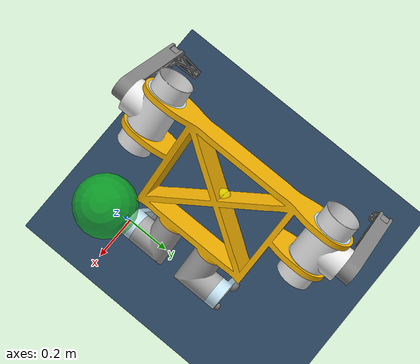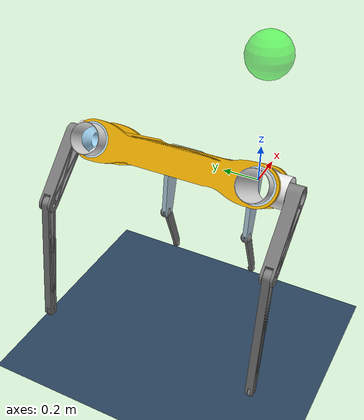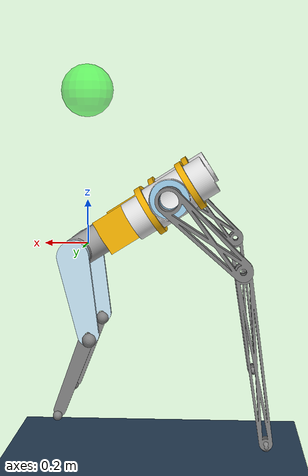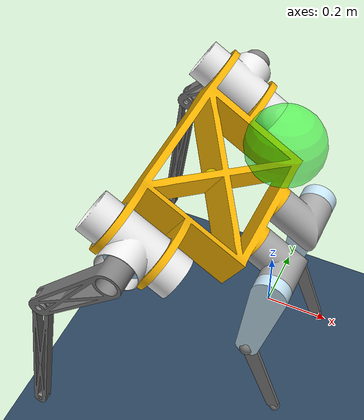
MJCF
<mujoco model="Pterosaur Jump">
  <include file="../common.xml"/>
  <include file="pterosaur_scene_modified.xml"/>

  <size memory="4M"/>

  <default>
    <default class="torque">
      <general gainprm="40" ctrllimited="true" ctrlrange="-1 1"/>
    </default>
    <default class="task">
      <site rgba="1 0 0 1" size=".02" group="5"/>
      <default class="flight">
        <site rgba="1 .3 .3 1" size="0.019" group="5"/>
      </default>
      <default class="stance">
        <site rgba=".3 1 .3 1" size=".018" group="4"/>
      </default>
    </default>
    <default class="prop">
      <geom type="box" rgba="0 0.4 1 1"/>
    </default>
  </default>
  <worldbody>
    <body name ="goal" mocap="true" pos ="0 0 0.7">
      <geom size="0.12" contype="0" conaffinity="0" rgba="0 1 0 0.5" group="2"/>
    </body>
  </worldbody>
  <custom>
    <!-- agent -->
    <text name="task_transition" data="Quadruped|Biped|Walk|Scramble|Flip|Launch|Launch Track" />
    <numeric name="agent_planner" data="2 " />
    <numeric name="agent_horizon" data="0.35" />
    <numeric name="agent_timestep" data="0.01" />
    <numeric name="sampling_spline_points" data="3" />
    <numeric name="sampling_trajectories" data="60"/>
    <numeric name="sampling_exploration" data="0.04" />
    <numeric name="gradient_spline_points" data="5" />

    <!-- residual -->
    <numeric name="residual_select_Gait" data="0"/>
    <text name="residual_list_Gait" data="Stand|Walk|Trot|Canter|Gallop"/>
    <numeric name="residual_select_Gait switch" data="0"/>
    <text name="residual_list_Gait switch" data="Manual|Automatic"/>
    <numeric name="residual_Cadence" data="2 0 4" />
    <numeric name="residual_Amplitude" data=".06 0 0.2" />
    <numeric name="residual_Duty ratio" data="0 0 1"/>
    <numeric name="residual_Walk speed" data="0 0 4"/>
    <numeric name="residual_Walk turn" data="0 -2 2"/>
    <numeric name="residual_select_Flip dir" data="0"/>
    <text name="residual_list_Flip dir" data="Back Flip|Front Flip"/>
    <numeric name="residual_select_Biped type" data="0"/>
    <text name="residual_list_Biped type" data="Foot Stand|Hand Stand"/>
    <numeric name="residual_Heading" data="0 -3.14 3.14" />
    <numeric name="residual_Arm posture" data=".03 0 1"/>
    <numeric name="residual_Launch speed" data="5 0 12"/>
    <numeric name="residual_Launch angle" data="30 0 60"/>
    <numeric name="residual_Ref start" data="0 0 1.9"/>
    <numeric name="residual_Push time" data="0 0 1.2"/>

    <!-- estimator -->
    <numeric name="estimator" data="0" />
    <numeric name="estimator_sensor_start" data="19" />
    <numeric name="estimator_number_sensor" data="21" />
    <numeric name="estimator_timestep" data="0.005" />
    <numeric name="batch_configuration_length" data="3" />
    <numeric name="batch_scale_prior" data="1.0e-3" />
  </custom>

  <sensor>
    <!-- cost -->
    <user name="Upright" dim="3" user="6 1 0 3 0.05" />
    <user name="Height" dim="1" user="6 1 0 3 0.04" />
    <user name="Position" dim="3" user="2 0.2 0 0.5 0.1" />
    <user name="LaunchVelocity" dim="1" user="0 1 0 0.5 0.1" />
    <user name="Gait" dim="4" user="6 0 0 10 0.03" />
    <user name="Balance" dim="2" user="2 0.2 0 0.3 0.1" />
    <user name="Effort" dim="12" user="0 0.05 0.0 0.1" />
    <user name="Posture" dim="15" user="0 0.1 0.0 1" />
    <user name="Orientation" dim="3" user="0 0 0 .03" />
    <user name="Angmom" dim="3" user="0 0 0 .03" />
    <user name="GroundContact" dim="4" user="0 0.5 0 1 0.1" />
    <!-- Launch Track: reference from launch_reference.xml, enabled in mode -->
    <user name="RefBasePos" dim="3" user="0 0 0 20" />
    <user name="RefBaseOri" dim="3" user="0 0 0 20" />
    <user name="RefJointPos" dim="12" user="0 0 0 20" />
    <user name="RefBaseVel" dim="6" user="0 0 0 5" />
    <user name="RefJointVel" dim="12" user="0 0 0 1" />
    <user name="RefTakeoff" dim="6" user="0 0 0 10" />
    <user name="Symmetry" dim="12" user="0 0 0 20" />
    <user name="Clearance" dim="6" user="0 0 0 50" />

    <!-- estimator measurements -->
    <framepos name="torso_pos" objtype="site" objname="com" />
    <framepos name="FR_pos" objtype="site" objname="FR" />
    <framepos name="FL_pos" objtype="site" objname="FL" />
    <framepos name="RR_pos" objtype="site" objname="RR" />
    <framepos name="RL_pos" objtype="site" objname="RL" />

    <jointpos name="pos_FR_hip_joint" joint="rightarm_shoulder1" />
    <jointpos name="pos_FR_thigh_joint" joint="rightarm_shoulder2" />
    <jointpos name="pos_FR_calf_joint" joint="rightarm_elbow" />
    <jointpos name="pos_FL_hip_joint" joint="leftarm_shoulder1" />
    <jointpos name="pos_FL_thigh_joint" joint="leftarm_shoulder2" />
    <jointpos name="pos_FL_calf_joint" joint="leftarm_elbow" />
    <jointpos name="pos_RR_hip_joint" joint="rightleg_hip1" />
    <jointpos name="pos_RR_thigh_joint" joint="rightleg_hip2" />
    <jointpos name="pos_RR_calf_joint" joint="rightleg_knee" />
    <jointpos name="pos_RL_hip_joint" joint="leftleg_hip1" />
    <jointpos name="pos_RL_thigh_joint" joint="leftleg_hip2" />
    <jointpos name="pos_RL_calf_joint" joint="leftleg_knee" />

    <touch name="FR_touch" site="FR"/>
    <touch name="FL_touch" site="FL"/>
    <touch name="RR_touch" site="RR"/>
    <touch name="RL_touch" site="RL"/>
    <touch name="RK_touch" site="RK"/>
    <touch name="LK_touch" site="LK"/>

    <!-- trace -->
    <framepos      name="trace0" objtype="site" objname="head"/>

    <!-- residual -->
    <subtreecom    name="torso_subtreecom" body="body"/>
    <subtreelinvel name="torso_subtreelinvel" body="body"/>
    <subtreelinvel name="torso_angmom" body="body"/>
    <subtreeangmom name="torso_subtreeangmom" body="body"/>
  </sensor>

  <keyframe>
    <key name="home"
         qpos="0 0 0.68
               0 0 0 0
               0 0 0
               0 0 0
               0 0 0
               0 0 0"/>
    <key name="crouch"
         qpos="0 0 0.3
               0 0 0 0
               0 -1.2 1.25
               0 -1.2 1.25
               0 -1.1 -1.75
         0 -1.1 -1.75"/>

    <key name="crouch2"
        qpos='0 0 0.379773
        1 0 0 0
        0 -0.89 1
        0 -0.89 1
        0 -0.67 -1.46
        0 -0.67 -1.46'/>

    <key name="crouch2og"
        qpos='0.011831 -0.000116004 0.379773
    0.999999 6.51715e-05 -0.00102298 -6.16775e-05
    0.000477862 -0.89019 1.02307
    -0.000578371 -0.889811 1.02252
    0.0106426 -0.670398 -1.45819
    -0.014095 -0.670603 -1.4568'/>

    <key name="pivot"
         qpos="0 0 1.075
         0.960050 0 -0.279830 0
                 0 0.120797 -0.610865
                 0 0.120797 -0.610865
                 0 1.320796 0.523599
         0 1.320796 0.523599"
       qvel="0 0 0 0 0 0
             0 2.5 0
             0 2.5 0
             0 0 0
             0 0 0"/>
  </keyframe>

  <!-- Launch Track reference (generated by npz_to_keyframes.py) -->
  <include file="launch_reference.xml"/>
</mujoco>

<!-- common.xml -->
<mujoco>

    <visual>
        <headlight ambient=".4 .4 .4" diffuse=".8 .8 .8" specular="0.1 0.1 0.1"/>
        <map znear=".01"/>
        <quality shadowsize="2048"/>
        <global elevation="-15"/>
    </visual>

    <asset>
        <texture name="blue_grid" type="2d" builtin="checker" rgb1=".02 .14 .44" rgb2=".27 .55 1" width="300" height="300" mark="edge" markrgb="1 1 1"/>
        <material name="blue_grid" texture="blue_grid" texrepeat="1 1" texuniform="true" reflectance=".2"/>

        <texture name="grey_grid" type="2d" builtin="checker" rgb1=".26 .26 .26" rgb2=".6 .6 .6" width="300" height="300" mark="edge" markrgb="1 1 1"/>
        <material name="grey_grid" texture="grey_grid" texrepeat="1 1" texuniform="true" reflectance=".2"/>
        <texture name="skybox" type="skybox" builtin="gradient" rgb1=".66 .79 1" rgb2=".9 .91 .93" width="800" height="800"/>

        <material name="self" rgba=".7 .5 .3 1"/>
        <material name="self_default" rgba=".7 .5 .3 1"/>
        <material name="self_highlight" rgba="0 .5 .3 1"/>
        <material name="effector" rgba=".7 .4 .2 1"/>
        <material name="effector_default" rgba=".7 .4 .2 1"/>
        <material name="effector_highlight" rgba="0 .5 .3 1"/>
        <material name="decoration" rgba=".2 .6 .3 1"/>
        <material name="eye" rgba="0 .2 1 1"/>
        <material name="target" rgba=".6 .3 .3 1"/>
        <material name="target_default" rgba=".6 .3 .3 1"/>
        <material name="target_highlight" rgba=".6 .3 .3 .4"/>
        <material name="site" rgba=".5 .5 .5 .3"/>
    </asset>

    <size memory="1M"/>

    <statistic extent="0.4" center="0.3 0.1 0"/>

    <visual>
        <quality shadowsize="8192"/>
        <global azimuth="180" elevation="-30"/>
    </visual>

    <default>
        <geom friction="1.0"/>
    </default>

    <compiler angle="radian" autolimits="true"/>

    <asset>
        <mesh name="apple" file="../../shared_assets/apple/apple.obj" />
        <mesh name="apple_contact0" file="../../shared_assets/apple/contact0.stl"  />
        <mesh name="apple_contact1" file="../../shared_assets/apple/contact1.stl"  />

        <mesh name="doorknob" file="../../shared_assets/doorknob/doorknob.obj" />

        <mesh name="flashlight" file="../../shared_assets/flashlight/flashlight.obj" />
        <mesh name="flashlight_contact0" file="../../shared_assets/flashlight/contact0.stl"  />
        <mesh name="flashlight_contact1" file="../../shared_assets/flashlight/contact1.stl"  />

        <mesh name="hammer" file="../../shared_assets/hammer/hammer.obj" />
        <mesh name="hammer_contact0" file="../../shared_assets/hammer/contact0.stl"  />
        <mesh name="hammer_contact1" file="../../shared_assets/hammer/contact1.stl"  />

        <mesh name="phone" file="../../shared_assets/phone/phone.obj" />
        <mesh name="phone_contact0" file="../../shared_assets/phone/contact0.stl"  />
        <mesh name="phone_contact1" file="../../shared_assets/phone/contact1.stl"  />
        <mesh name="phone_contact2" file="../../shared_assets/phone/contact2.stl"  />

        <mesh name="stapler" file="../../shared_assets/stapler/stapler.obj" />
        <mesh name="stapler_contact0" file="../../shared_assets/stapler/contact0.stl"  />
        <mesh name="stapler_contact1" file="../../shared_assets/stapler/contact1.stl"  />
        <mesh name="stapler_contact2" file="../../shared_assets/stapler/contact2.stl"  />
        <mesh name="stapler_contact3" file="../../shared_assets/stapler/contact3.stl"  />
        <mesh name="stapler_contact4" file="../../shared_assets/stapler/contact4.stl"  />

        <mesh name="waterbottle" file="../../shared_assets/waterbottle/waterbottle.obj" />
        <mesh name="waterbottle_contact0" file="../../shared_assets/waterbottle/contact0.stl"  />
        <mesh name="waterbottle_contact1" file="../../shared_assets/waterbottle/contact1.stl"  />
    </asset>

</mujoco>

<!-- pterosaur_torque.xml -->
<!-- Generated using onshape-to-robot -->
<!-- Onshape https://cad.onshape.com/documents/10983e84519d457ae82440ea/w/286bda59dae2fbf061500275/e/1ab19f16b069914ec1cc48d7 -->
<mujoco model="pterosaur">
  <compiler angle="radian" meshdir="assets" autolimits="true"/>
  <option integrator="implicit" timestep="0.01"/>
  <default>
    <default class="pterosaur">
      <joint frictionloss="0.1" armature="0.005"/>
      <default class="visual">`
        <geom type="mesh" contype="0" conaffinity="0" group="2"/>
      </default>
      <default class="collision">
        <geom group="3"/>
      </default>
      <default class="foot">
        <geom size="0.02" pos= "0 0 -0.2" type="sphere" priority="1" solimp="0.015 1 0.031" condim="6" friction="1.2 0.02 0.01" contype="2" conaffinity="1"/>
      </default>
    </default>
  </default>
  <worldbody>
    <!-- Link body -->
    <body name="body" pos="0 0 0" quat="1 0 0 0" childclass="pterosaur">
      <freejoint name="body_freejoint"/>
      <site name="com" rgba="1 0 0 1" pos="-0.329162 0.2607 0.205848" size="0.001"/>
      <geom name="height_probe_visual" type="sphere" size="0.03"
        pos="-0.329162 0.2607 0.205848" contype="0" conaffinity="0"
        rgba="1 1 0 0.6" group="2"/>
      <site name="head" pos="-0.029162 0.2607 0.205848" class="task"/>
      <inertial pos="-0.329162 0.2607 0.205848" mass="21.9159" fullinertia="1.49474 0.542959 1.69386 -0 0.204502 0"/>
      <!-- Part body -->
      <geom type="mesh" class="visual" pos="-1.16424 0.2607 0.72808" quat="0.618511 -0.342701 -0.342701 0.618511" mesh="body" material="body_material"/>
      <geom type="mesh" class="collision" pos="-1.16424 0.2607 0.72808" quat="0.618511 -0.342701 -0.342701 0.618511" mesh="body" material="body_material"/>
      <!-- Part housing_bearing -->
      <geom type="mesh" class="visual" pos="-1.16424 0.2607 0.72808" quat="0.618511 -0.342701 -0.342701 0.618511" mesh="housing_bearing" material="housing_bearing_material"/>
      <geom type="mesh" class="collision" pos="-1.16424 0.2607 0.72808" quat="0.618511 -0.342701 -0.342701 0.618511" mesh="housing_bearing" material="housing_bearing_material"/>
      <!-- Part housing_bearing_2 -->
      <geom type="mesh" class="visual" pos="-1.31895 1.12179 0.824836" quat="0.618511 -0.342701 -0.342701 0.618511" mesh="housing_bearing" material="housing_bearing_material"/>
      <geom type="mesh" class="collision" pos="-1.31895 1.12179 0.824836" quat="0.618511 -0.342701 -0.342701 0.618511" mesh="housing_bearing" material="housing_bearing_material"/>
      <!-- Part housing_bearing_3 -->
      <geom type="mesh" class="visual" pos="-1.31895 0.2607 0.824836" quat="0.618511 -0.342701 -0.342701 0.618511" mesh="housing_bearing" material="housing_bearing_material"/>
      <geom type="mesh" class="collision" pos="-1.31895 0.2607 0.824836" quat="0.618511 -0.342701 -0.342701 0.618511" mesh="housing_bearing" material="housing_bearing_material"/>
      <!-- Part housing_bearing_4 -->
      <geom type="mesh" class="visual" pos="-1.16424 1.12179 0.72808" quat="0.618511 -0.342701 -0.342701 0.618511" mesh="housing_bearing" material="housing_bearing_material"/>
      <geom type="mesh" class="collision" pos="-1.16424 1.12179 0.72808" quat="0.618511 -0.342701 -0.342701 0.618511" mesh="housing_bearing" material="housing_bearing_material"/>
      <!-- Link smaller_housing -->
      <body name="smaller_housing" pos="-0.342251 -0.169846 0.214034" quat="0.484652 0 0.874707 -0">
        <!-- Joint from body to smaller_housing -->
        <joint axis="0 0 1" name="leftarm_shoulder1" type="hinge"/>
        <inertial pos="-1.24807e-06 0.00682513 -0.0787398" mass="1.343" fullinertia="0.0135155 0.013795 0.00927768 1.6788e-08 5.6242e-08 3.9866e-08"/>
        <!-- Part smaller_housing -->
        <geom type="mesh" class="visual" pos="0.430546 0 -0.969486" quat="0 1 0 0" mesh="smaller_housing" material="smaller_housing_material"/>
        <!-- Link bevel_out -->
        <body name="bevel_out" pos="0 -0.0762 -0.07874" quat="0.0909266 0.0909266 -0.701236 0.701236">
          <!-- Joint from smaller_housing to bevel_out -->
          <joint axis="0 0 1" name="leftarm_shoulder2" type="hinge"/>
          <inertial pos="-0.0753731 -0 0.0347345" mass="4.75962" fullinertia="0.0153834 0.0797297 0.0750715 -0 0.0171537 0"/>
          <!-- Part humerus -->
          <geom type="mesh" class="visual" pos="0.430546 -0.890746 -0.0762" quat="0.707107 0.707107 -0 -0" mesh="humerus" material="humerus_material"/>
          <geom type="mesh" class="collision" pos="0.430546 -0.890746 -0.0762" quat="0.707107 0.707107 -0 -0" mesh="humerus" material="humerus_material"/>
          <!-- Part bevel_out -->
          <geom type="mesh" class="visual" pos="0.430546 -0.890746 -0.0762" quat="0.707107 0.707107 -0 -0" mesh="bevel_out" material="bevel_out_material"/>
          <!-- Link radius_and_ulna -->
          <body name="radius_and_ulna" pos="-0.381 -0 0.1016" quat="0.943004 -0 0 0.332781">
            <!-- Joint from bevel_out to radius_and_ulna -->
            <joint axis="0 0 1" name="leftarm_elbow" type="hinge"/>
            <inertial pos="-0.306294 0 -0.01905" mass="1.60866" fullinertia="0.000762134 0.0693551 0.0697199 0 0 -0"/>
            <!-- Part radius_and_ulna -->
            <geom type="mesh" class="visual" pos="0.811546 -0.890746 -0.1778" quat="0.707107 0.707107 0 0" mesh="radius_and_ulna" material="radius_and_ulna_material"/>
            <geom type="mesh" class="collision" pos="0.811546 -0.890746 -0.1778" quat="0.707107 0.707107 0 0" mesh="radius_and_ulna" material="radius_and_ulna_material"/>
            <geom name="FL" size="0.02" pos= "-0.675 0 -0.02" type="sphere" priority="1" solimp="0.015 1 0.031" condim="6" friction="1 0.02 0.01" contype="2" conaffinity="1"/>
            <site name="FL" type="sphere" size="0.02" pos="-0.675 0 -0.02"/>
            <!-- Link finger -->
            <!--body name="finger" pos="-0.6604 0 -0.0127" quat="0 0.224528 0.974468 -0"-->
              <!-- Joint from radius_and_ulna to finger -->
              <!--joint axis="0 0 1" name="leftarm_finger" type="hinge"/-->
              <!--inertial pos="-0.346533 0.00351695 -0.00634993" mass="0.0823581" fullinertia="1.11507e-05 0.00430132 0.00431156 0.000126744 9.11e-10 -8.1e-11"/-->
              <!-- Part finger -->
              <!--geom type="mesh" class="visual" pos="1.47195 -0.890746 -0.1651" quat="0.707107 0.707107 0 -0" mesh="finger" material="finger_material"/-->
            <!--/body-->
          </body>
        </body>
      </body>
      <!-- Link smaller_housing_2 -->
      <body name="smaller_housing_2" pos="-0.342251 0.691246 0.214034" quat="0 0.874707 -0 0.484652">
        <!-- Joint from body to smaller_housing_2 -->
        <joint axis="0 0 1" name="rightarm_shoulder1" type="hinge"/>
        <inertial pos="-1.24807e-06 0.00682513 -0.0787398" mass="1.343" fullinertia="0.0135155 0.013795 0.00927768 1.6788e-08 5.6242e-08 3.9866e-08"/>
        <!-- Part smaller_housing_2 -->
        <geom type="mesh" class="visual" pos="0.430546 0 -0.969486" quat="0 1 0 0" mesh="smaller_housing" material="smaller_housing_material"/>
        <!-- Link bevel_out_2 -->
        <body name="bevel_out_2" pos="0 -0.0762 -0.07874" quat="0.707107 -0.707107 -0 -0">
          <!-- Joint from smaller_housing_2 to bevel_out_2 -->
          <joint axis="0 0 1" name="rightarm_shoulder2" type="hinge"/>
          <inertial pos="-0.0728804 0.0192235 -0.0347345" mass="4.75962" fullinertia="0.019569 0.0755441 0.0750715 0.0158684 -0.0165864 0.00437495"/>
          <!-- Part humerus_2 -->
          <geom type="mesh" class="visual" pos="0.643487 0.751481 0.0762" quat="0.701236 -0.701236 0.0909266 -0.0909266" mesh="humerus" material="humerus_material"/>
          <geom type="mesh" class="collision" pos="0.643487 0.751481 0.0762" quat="0.701236 -0.701236 0.0909266 -0.0909266" mesh="humerus" material="humerus_material"/>
          <!-- Part bevel_out_2 -->
          <geom type="mesh" class="visual" pos="-0.751481 0.643487 0.0762" quat="0.560144 -0.560144 -0.431554 0.431554" mesh="bevel_out" material="bevel_out_material"/>
          <!-- Link radius_and_ulna_2 -->
          <body name="radius_and_ulna_2" pos="-0.3684 0.0971719 -0.0635" quat="0.977967 0 -0 0.208758">
            <!-- Joint from bevel_out_2 to radius_and_ulna_2 -->
            <joint axis="0 0 1" name="rightarm_elbow" type="hinge"/>
            <inertial pos="-0.306294 0 -0.01905" mass="1.60866" fullinertia="0.000762134 0.0693551 0.0697199 0 -0 -0"/>
            <!-- Part radius_and_ulna_2 -->
            <geom type="mesh" class="visual" pos="0.811546 -0.890746 -0.1778" quat="0.707107 0.707107 0 -0" mesh="radius_and_ulna" material="radius_and_ulna_material"/>
            <geom type="mesh" class="collision" pos="0.811546 -0.890746 -0.1778" quat="0.707107 0.707107 0 -0" mesh="radius_and_ulna" material="radius_and_ulna_material"/>
            <geom name="FR" size="0.02" pos="-0.675 0 -0.02" type="sphere" priority="1" solimp="0.015 1 0.031" condim="6" friction="1 0.02 0.01" contype="2" conaffinity="1"/>
            <site name="FR" type="sphere" size="0.02" pos="-0.675 0 -0.02" />
            <!-- Link finger_2 -->
            <!--body name="finger_2" pos="-0.6604 0 -0.0127" quat="0 0.224528 0.974468 -0"-->
              <!-- Joint from radius_and_ulna_2 to finger_2 -->
              <!--joint axis="0 0 1" name="rightarm_finger" type="hinge"/-->
              <!--inertial pos="-0.346533 0.00351695 -0.00634993" mass="0.0823581" fullinertia="1.11507e-05 0.00430132 0.00431156 0.000126744 9.11e-10 -8.1e-11"/-->
              <!-- Part finger_2 -->
              <!--geom type="mesh" class="visual" pos="1.47195 -0.890746 -0.1651" quat="0.707107 0.707107 0 -0" mesh="finger" material="finger_material"/-->
            <!--/body-->
          </body>
        </body>
      </body>
      <!-- Link leg_motor_1 -->
      <body name="leg_motor_1" pos="-0.124306 0.1575 0.0777372" quat="0.618511 -0.342701 -0.342701 0.618511">
        <!-- Joint from body to leg_motor_1 -->
        <joint axis="0 0 1" name="leftleg_hip1" type="hinge"/>
        <inertial pos="-0.0085028 -1.1347e-08 -0.0878363" mass="2.7422" fullinertia="0.0167106 0.0181836 0.00941714 3.926e-09 -0.00137046 -7.7e-10"/>
        <!-- Part hip -->
        <geom type="mesh" class="visual" pos="0.1032 0 1.22654" quat="1 0 -0 0" mesh="hip" material="hip_material"/>
        <geom type="mesh" class="collision" pos="0.1032 0 1.22654" quat="1 0 -0 0" mesh="hip" material="hip_material"/>
        <!-- Part leg_motor_1 -->
        <geom type="mesh" class="visual" pos="0.1032 0 1.22654" quat="1 -0 0 0" mesh="leg_motor_1" material="leg_motor_1_material"/>
        <geom type="mesh" class="collision" pos="0.1032 0 1.22654" quat="1 -0 0 0" mesh="leg_motor_1" material="leg_motor_1_material"/>
        <!-- Link leg_motor_2 -->
        <body name="leg_motor_2" pos="-0.1075 -0 -0.146612" quat="0.399172 -0.583663 -0.399172 0.583663">
          <!-- Joint from leg_motor_1 to leg_motor_2 -->
          <joint axis="0 0 1" name="leftleg_hip2" type="hinge"/>
          <inertial pos="0.0727822 -0 0.0216101" mass="3.21492" fullinertia="0.0045526 0.0395144 0.0412537 0 -0.00371806 -0"/>
          <!-- Part femur -->
          <geom type="mesh" class="visual" pos="-0 -1.37315 -0.2107" quat="0.5 0.5 0.5 -0.5" mesh="femur" material="femur_material"/>
          <geom type="mesh" class="collision" pos="-0 -1.37315 -0.2107" quat="0.5 0.5 0.5 -0.5" mesh="femur" material="femur_material"/>
          <!-- Part leg_motor_3 -->
          <geom type="mesh" class="visual" pos="-0 -1.37315 -0.2107" quat="0.5 0.5 0.5 -0.5" mesh="leg_motor_3" material="leg_motor_3_material"/>
          <geom type="mesh" class="collision" pos="-0 -1.37315 -0.2107" quat="0.5 0.5 0.5 -0.5" mesh="leg_motor_3" material="leg_motor_3_material"/>
          <!-- Part leg_motor_2 -->
          <geom type="mesh" class="visual" pos="-0 -1.37315 -0.2107" quat="0.5 0.5 0.5 -0.5" mesh="leg_motor_2" material="leg_motor_2_material"/>
          <geom type="mesh" class="collision" pos="-0 -1.37315 -0.2107" quat="0.5 0.5 0.5 -0.5" mesh="leg_motor_2" material="leg_motor_2_material"/>
          <!-- Knee joint touch sensor visualization -->
          <geom name="LK_visual" type="sphere" size="0.03" pos="0.353 0 0.033" rgba="0 1 1 0.3"/>
          <!-- Knee joint collision sensor (ground only) -->
          <geom name="LK" type="sphere" size="0.03" pos="0.353 0 0.033" contype="2" conaffinity="1" priority="1" solimp="0.015 1 0.031" condim="6" friction="1 0.02 0.01"/>
          <site name="LK" type="sphere" size="0.03" pos="0.353 0 0.033"/>
          <!-- Link tibia -->
          <body name="tibia" pos="0.3302 -0 0.03115" quat="0 0.962486 0.271331 0">
            <!-- Joint from leg_motor_2 to tibia -->
            <joint axis="0 0 1" name="leftleg_knee" type="hinge"/>
            <inertial pos="0.164731 0 -0.00635" mass="0.440746" fullinertia="0.000126716 0.00537275 0.00548761 0 0 0"/>
            <geom name="HL" class="foot" pos= "0.3681 0 0"/>
            <site name="RL" type="sphere" size="0.02" pos="0.3681 0 0"/>
            <!-- Part tibia -->
            <geom type="mesh" class="visual" pos="-0.3302 1.37315 0.24185" quat="0.5 -0.5 -0.5 -0.5" mesh="tibia" material="tibia_material"/>
            <geom type="mesh" class="collision" pos="-0.3302 1.37315 0.24185" quat="0.5 -0.5 -0.5 -0.5" mesh="tibia" material="tibia_material"/>
          </body>
        </body>
      </body>
      <!-- Link hip -->
      <body name="hip" pos="-0.124306 0.3639 0.0777372" quat="0.618511 -0.342701 -0.342701 0.618511">
        <!-- Joint from body to hip -->
        <joint axis="0 0 1" name="rightleg_hip1" type="hinge"/>
        <inertial pos="0.0085028 1.1347e-08 -0.0878363" mass="2.7422" fullinertia="0.0167106 0.0181836 0.00941714 3.926e-09 0.00137046 7.7e-10"/>
        <!-- Part leg_motor_1_2 -->
        <geom type="mesh" class="visual" pos="0.1032 0 1.22654" quat="1 0 0 0" mesh="leg_motor_1" material="leg_motor_1_material"/>
        <geom type="mesh" class="collision" pos="0.1032 0 1.22654" quat="1 0 0 0" mesh="leg_motor_1" material="leg_motor_1_material"/>
        <!-- Part hip_2 -->
        <geom type="mesh" class="visual" pos="-0.1032 0 1.22654" quat="0 0 0 1" mesh="hip" material="hip_material"/>
        <geom type="mesh" class="collision" pos="-0.1032 0 1.22654" quat="0 0 0 1" mesh="hip" material="hip_material"/>
        <!-- Link femur -->
        <body name="femur" pos="0.1075 0 -0.146612" quat="0.5 0.5 -0.5 -0.5">
          <!-- Joint from hip to femur -->
          <joint axis="0 0 1" name="rightleg_hip2" type="hinge"/>
          <inertial pos="-0.0678277 -0.0263943 -0.0216101" mass="3.21492" fullinertia="0.00915055 0.0349165 0.0412537 -0.0118157 -0.00346496 -0.00134835"/>
          <!-- Part leg_motor_2_2 -->
          <geom type="mesh" class="visual" pos="-0.497971 1.27968 0.2107" quat="0.583663 -0.399172 -0.583663 -0.399172" mesh="leg_motor_2" material="leg_motor_2_material"/>
          <geom type="mesh" class="collision" pos="-0.497971 1.27968 0.2107" quat="0.583663 -0.399172 -0.583663 -0.399172" mesh="leg_motor_2" material="leg_motor_2_material"/>
          <!-- Part femur_2 -->
          <geom type="mesh" class="visual" pos="0.497971 -1.27968 0.2107" quat="0.399172 0.583663 -0.399172 0.583663" mesh="femur" material="femur_material"/>
          <geom type="mesh" class="collision" pos="0.497971 -1.27968 0.2107" quat="0.399172 0.583663 -0.399172 0.583663" mesh="femur" material="femur_material"/>
          <!-- Part leg_motor_3_2 -->
          <geom type="mesh" class="visual" pos="-0.497971 1.27968 0.2107" quat="0.583663 -0.399172 -0.583663 -0.399172" mesh="leg_motor_3" material="leg_motor_3_material"/>
          <geom type="mesh" class="collision" pos="-0.497971 1.27968 0.2107" quat="0.583663 -0.399172 -0.583663 -0.399172" mesh="leg_motor_3" material="leg_motor_3_material"/>
          <!-- Knee joint touch sensor visualization -->
          <geom name="RK_visual" type="sphere" size="0.03" pos="-0.329 -0.128 -0.047" rgba="0 1 1 0.3"/>
          <!-- Knee joint collision sensor (ground only) -->
          <geom name="RK" type="sphere" size="0.03" pos="-0.329 -0.128 -0.047" contype="2" conaffinity="1" priority="1" solimp="0.015 1 0.031" condim="6" friction="1 0.02 0.01"/>
          <site name="RK" type="sphere" size="0.03" pos="-0.329 -0.128 -0.047"/>
          <!-- Link tibia_2 -->
          <body name="tibia_2" pos="-0.307722 -0.119746 -0.04385" quat="0 0.444243 -0.895906 -0">
            <!-- Joint from femur to tibia_2 -->
            <joint axis="0 0 1" name="rightleg_knee" type="hinge"/>
            <inertial pos="0.164731 -0 -0.00635" mass="0.440746" fullinertia="0.000126716 0.00537275 0.00548761 -0 -0 -0"/>
            <geom name="HR" class="foot" pos="0.3681 0 0"/>
            <site name="RR" type="sphere" size="0.02" pos="0.3681 0 0"/>
            <!-- Part tibia_2 -->
            <geom type="mesh" class="visual" pos="-0.3302 -1.37315 -0.25455" quat="0.5 0.5 0.5 -0.5" mesh="tibia" material="tibia_material"/>
            <geom type="mesh" class="collision" pos="-0.3302 -1.37315 -0.25455" quat="0.5 0.5 0.5 -0.5" mesh="tibia" material="tibia_material"/>
          </body>
        </body>
      </body>
    </body>
  </worldbody>
  <asset>
    <mesh file="femur.stl"/>
    <mesh file="hip.stl"/>
    <mesh file="housing_bearing.stl"/>
    <mesh file="smaller_housing.stl"/>
    <mesh file="finger.stl"/>
    <mesh file="body.stl"/>
    <mesh file="humerus.stl"/>
    <mesh file="tibia.stl"/>
    <mesh file="radius_and_ulna.stl"/>
    <mesh file="bevel_out.stl"/>
    <mesh file="leg_motor_2.stl"/>
    <mesh file="leg_motor_1.stl"/>
    <mesh file="leg_motor_3.stl"/>
    <material name="body_material" rgba="0.980392 0.713725 0.00392157 1"/>
    <material name="housing_bearing_material" rgba="0.768627 0.886275 0.952941 1"/>
    <material name="smaller_housing_material" rgba="0.917647 0.917647 0.917647 1"/>
    <material name="humerus_material" rgba="0.498039 0.498039 0.498039 1"/>
    <material name="bevel_out_material" rgba="0.615686 0.811765 0.929412 1"/>
    <material name="radius_and_ulna_material" rgba="0.498039 0.498039 0.498039 1"/>
    <material name="finger_material" rgba="0.980392 0.713725 0.00392157 1"/>
    <material name="hip_material" rgba="0.647059 0.647059 0.647059 1"/>
    <material name="leg_motor_1_material" rgba="0.615686 0.811765 0.929412 1"/>
    <material name="femur_material" rgba="0.768627 0.886275 0.952941 1"/>
    <material name="leg_motor_3_material" rgba="0.917647 0.917647 0.917647 1"/>
    <material name="leg_motor_2_material" rgba="0.231373 0.380392 0.705882 1"/>
    <material name="tibia_material" rgba="0.498039 0.498039 0.498039 1"/>
  </asset>
  <actuator>
    <general class="pterosaur" name="leftarm_shoulder1" joint="leftarm_shoulder1" ctrllimited ="true" gainprm="100" ctrlrange="-1 1"/>
    <general class="pterosaur" name="leftarm_shoulder2" joint="leftarm_shoulder2" ctrllimited ="true" gainprm="100" ctrlrange="-1 1"/>
    <general class="pterosaur" name="leftarm_elbow" joint="leftarm_elbow" ctrllimited ="true" gainprm="40" ctrlrange="-1 1"/>
    <general class="pterosaur" name="rightarm_shoulder1" joint="rightarm_shoulder1" ctrllimited ="true" gainprm="100" ctrlrange="-1 1"/>
    <general class="pterosaur" name="rightarm_shoulder2" joint="rightarm_shoulder2" ctrllimited ="true" gainprm="100" ctrlrange="-1 1" />
    <general class="pterosaur" name="rightarm_elbow" joint="rightarm_elbow" ctrllimited ="true" gainprm="40" ctrlrange="-1 1"/>
    <general class="pterosaur" name="leftleg_hip1" joint="leftleg_hip1"  ctrllimited ="true" gainprm="50" ctrlrange="-1 1"/>
    <general class="pterosaur" name="leftleg_hip2" joint="leftleg_hip2" ctrllimited ="true" gainprm="50" ctrlrange="-1 1"/>
    <general class="pterosaur" name="leftleg_knee" joint="leftleg_knee"  ctrllimited ="true" gainprm= "25" ctrlrange="-1 1"/>
    <general class="pterosaur" name="rightleg_hip1" joint="rightleg_hip1" ctrllimited ="true" gainprm="50" ctrlrange="-1 1"/>
    <general class="pterosaur" name="rightleg_hip2" joint="rightleg_hip2"  ctrllimited ="true" gainprm="50" ctrlrange="-1 1"/>
    <general class="pterosaur" name="rightleg_knee" joint="rightleg_knee" ctrllimited ="true" gainprm="25"  ctrlrange="-1 1"/>
  </actuator>
</mujoco>

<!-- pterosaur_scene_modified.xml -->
<mujoco model="Pterosaur Scene">
    <include file="pterosaur_torque.xml" />

    <visual>
        <headlight diffuse="0.6 0.6 0.6" ambient="0.3 0.3 0.3" specular="0 0 0" />
        <rgba haze="0.15 0.25 0.35 1" />
        <global azimuth="160" elevation="-20" />
    </visual>

    <asset>
        <texture type="skybox" builtin="gradient" rgb1="0.3 0.5 0.7" rgb2="0 0 0" width="512"
            height="3072" />
        <texture type="2d" name="groundplane" builtin="checker" mark="edge" rgb1="0.2 0.3 0.4"
            rgb2="0.1 0.2 0.3"
            markrgb="0.8 0.8 0.8" width="300" height="300" />
        <material name="groundplane" texture="groundplane" texuniform="true" texrepeat="5 5"
            reflectance="0.2" />
    </asset>

    <worldbody>
        <light pos="0 0 3.5" dir="0 0 -1" directional="true" />
        <geom name="floor" size="0 0 0.05" pos="0 0 -1" type="plane" material="groundplane" contype="1" conaffinity="3" />
    </worldbody>
</mujoco>

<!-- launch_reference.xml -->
<!-- Generated by npz_to_keyframes.py from launch.npz. Do not edit by hand. -->
<mujoco>
  <custom>
    <numeric name="launch_ref_takeoff" data="1.94"/>
    <numeric name="launch_ref_hands_contact" data="1 1 1 1 1 1 1 1 1 1 1 1 1 1 1 1 1 1 1 1 1 1 1 1 1 1 1 1 1 1 1 1 1 1 1 1 1 1 1 1 1 1 1 1 1 1 1 1 1 1 1 1 1 1 1 1 1 1 1 1 1 1 1 1 1 1 1 1 1 1 1 1 1 1 1 1 1 1 1 1 1 1 1 1 1 1 1 1 1 1 1 1 1 1 1 1 1 1 1 1 1 1 1 1 1 1 1 1 1 1 1 1 1 1 1 1 1 1 1 1 1 1 1 1 1 1 1 1 1 1 1 1 1 1 1 1 1 1 1 1 1 1 1 1 1 1 1 1 1 1 1 1 1 1 1 1 1 1 1 1 1 1 1 1 1 1 1 1 1 1 1 1 1 1 1 1 1 1 1 1 1 1 1 1 1 1 1 1 1 1 1 1 1 1 0 0 0 0 0 0 0 0 0 0 0 0 0 0 0 0 0 0 0 0 0 0 0 0 0 0 0 0 0 0 0 0 0 0 0 0 0 0 0 0 0 0 0 0 0 0 0 0 0 0 0 0 0 0 0 0 0 0 0 0 0 0 0 0 0 0 0"/>
    <numeric name="launch_ref_feet_contact" data="1 1 1 1 1 1 1 1 1 1 1 1 1 1 1 1 1 1 1 1 1 1 1 1 1 1 1 1 1 1 1 1 1 1 1 1 1 1 1 1 1 1 1 1 1 1 1 1 1 1 1 1 1 1 1 1 1 1 1 1 1 1 1 1 1 1 1 1 1 1 1 1 1 1 1 1 1 1 1 1 1 1 1 1 1 1 1 1 1 1 1 1 1 1 1 1 1 1 1 1 1 1 1 1 1 1 1 1 1 1 1 1 1 1 1 1 1 1 1 1 1 1 1 1 1 1 1 1 1 1 1 1 1 1 1 1 1 1 1 1 1 1 1 1 1 1 1 1 1 1 1 1 1 1 1 1 1 1 1 0 0 0 0 0 0 0 0 0 0 0 0 0 0 0 0 0 0 0 0 0 0 0 0 0 0 0 0 0 0 0 0 0 0 0 0 0 0 0 0 0 0 0 0 0 0 0 0 0 0 0 0 0 0 0 0 0 0 0 0 0 0 0 0 0 0 0 0 0 0 0 0 0 0 0 0 0 0 0 0 0 0 0 0 0 0 0 0 0 0 0 0 0 0 0 0 0 0 0 0 0 0"/>
  </custom>
  <keyframe>
    <key name="launch_ref_000" time="0"
         qpos="0.782281 0 -0.482918 1 0 0.000233676 0 -0.00688152 -0.544716 0.68158 0.00461246 -0.545537 0.682778 0.0143943 -0.664503 -1.00308 0.0154405 -0.66844 -1.01826"
         qvel="0.00102535 0 0.000303325 0 -0.00441806 0 -7.9136e-06 -0.00844339 0.00465784 5.30663e-06 -0.00844545 0.00465665 -6.35899e-05 -0.00569837 0.00132945 -6.89862e-05 -0.00576874 0.00132853"/>
    <key name="launch_ref_001" time="0.01"
         qpos="0.782292 0 -0.482915 1 0 0.000211586 0 -0.0068816 -0.544801 0.681627 0.00461252 -0.545621 0.682825 0.0143936 -0.66456 -1.00307 0.0154398 -0.668498 -1.01825"
         qvel="0.00134893 0 0.000394705 0 -0.00581119 0 -1.04397e-05 -0.0111174 0.00613885 7.00057e-06 -0.0111201 0.00613728 -8.35177e-05 -0.00750554 0.00173133 -9.06043e-05 -0.00759802 0.00173013"/>
    <key name="launch_ref_002" time="0.02"
         qpos="0.782308 0 -0.48291 1 0 0.000175564 0 -0.00688173 -0.544939 0.681703 0.0046126 -0.545759 0.682901 0.0143926 -0.664653 -1.00304 0.0154387 -0.668592 -1.01823"
         qvel="0.00215471 0 0.000619302 0 -0.00928209 0 -1.67601e-05 -0.0177878 0.00983833 1.12389e-05 -0.0177921 0.00983582 -0.000133045 -0.0120141 0.00272018 -0.000144333 -0.0121617 0.00271823"/>
    <key name="launch_ref_003" time="0.03"
         qpos="0.782335 0 -0.482902 1 0 0.000118765 0 -0.00688193 -0.545157 0.681823 0.00461274 -0.545977 0.683021 0.014391 -0.6648 -1.00301 0.0154369 -0.668741 -1.01819"
         qvel="0.00333026 0 0.00093919 0 -0.0143468 0 -2.605e-05 -0.0275428 0.0152598 1.74684e-05 -0.0275495 0.0152559 -0.000205035 -0.0186103 0.00413153 -0.000222432 -0.0188381 0.00412851"/>
    <key name="launch_ref_004" time="0.04"
         qpos="0.782375 0 -0.482891 1 0 3.20958e-05 0 -0.00688225 -0.54549 0.682008 0.00461295 -0.54631 0.683206 0.0143885 -0.665025 -1.00296 0.0154342 -0.668969 -1.01814"
         qvel="0.00498416 0 0.00137696 0 -0.0214725 0 -3.92308e-05 -0.0413013 0.0229229 2.63071e-05 -0.0413114 0.0229171 -0.000305852 -0.0279182 0.00606804 -0.000331801 -0.0282585 0.00606353"/>
    <key name="launch_ref_005" time="0.05"
         qpos="0.782434 0 -0.482875 1 0 -9.59606e-05 0 -0.00688272 -0.545983 0.682282 0.00461327 -0.546803 0.68348 0.0143848 -0.665358 -1.00289 0.0154303 -0.669306 -1.01807"
         qvel="0.00722755 0 0.00195235 0 -0.0311398 0 -5.72947e-05 -0.0600192 0.0333726 3.84203e-05 -0.0600339 0.0333641 -0.000441839 -0.0405862 0.00862176 -0.00047932 -0.0410789 0.00861519"/>
    <key name="launch_ref_006" time="0.06"
         qpos="0.78252 0 -0.482852 1 0 -0.000279303 0 -0.00688339 -0.54669 0.682675 0.00461372 -0.547511 0.683873 0.0143796 -0.665837 -1.00279 0.0154247 -0.66979 -1.01797"
         qvel="0.0101622 0 0.00267804 0 -0.0437881 0 -8.12172e-05 -0.0845858 0.0471211 5.4462e-05 -0.0846064 0.0471092 -0.000618515 -0.0572189 0.0118563 -0.000670975 -0.0579103 0.0118471"/>
    <key name="launch_ref_007" time="0.07"
         qpos="0.782638 0 -0.482821 1 0 -0.000533842 0 -0.00688434 -0.547674 0.683224 0.00461436 -0.548495 0.684422 0.0143725 -0.666503 -1.00265 0.0154169 -0.670464 -1.01784"
         qvel="0.0138645 0 0.00355452 0 -0.0597472 0 -0.000111852 -0.115695 0.0645768 7.50049e-05 -0.115723 0.0645605 -0.000839478 -0.0782891 0.0157849 -0.000910664 -0.07923 0.0157723"/>
    <key name="launch_ref_008" time="0.08"
         qpos="0.782797 0 -0.482781 1 0 -0.000876774 0 -0.00688563 -0.549004 0.683967 0.00461522 -0.549825 0.685164 0.0143629 -0.667403 -1.00247 0.0154064 -0.671375 -1.01766"
         qvel="0.0183681 0 0.00456599 0 -0.0791666 0 -0.000149815 -0.15371 0.0859675 0.000100462 -0.153748 0.0859458 -0.00110535 -0.104043 0.020353 -0.00119905 -0.105286 0.0203363"/>
    <key name="launch_ref_009" time="0.09"
         qpos="0.783005 0 -0.48273 0.999999 0 -0.00132551 0 -0.00688734 -0.550749 0.684944 0.00461637 -0.55157 0.686141 0.0143504 -0.668584 -1.00225 0.0153929 -0.67257 -1.01743"
         qvel="0.0236508 0 0.00567693 0 -0.101953 0 -0.000195369 -0.198539 0.111269 0.000131009 -0.198587 0.111242 -0.00141291 -0.134418 0.0254229 -0.00153265 -0.136013 0.0254013"/>
    <key name="launch_ref_010" time="0.1"
         qpos="0.78327 0 -0.482667 0.999998 0 -0.0018963 0 -0.00688954 -0.552975 0.686192 0.00461784 -0.553797 0.687389 0.0143346 -0.670091 -1.00196 0.0153758 -0.674095 -1.01715"
         qvel="0.0296243 0 0.00683091 0 -0.127728 0 -0.000248338 -0.249553 0.14016 0.000166529 -0.249614 0.140125 -0.00175458 -0.16899 0.0307679 -0.0019032 -0.170979 0.0307409"/>
    <key name="launch_ref_011" time="0.11"
         qpos="0.783598 0 -0.482593 0.999997 0 -0.00260278 0 -0.0068923 -0.55574 0.687747 0.0046197 -0.556562 0.688943 0.0143153 -0.671963 -1.00163 0.0153548 -0.67599 -1.01681"
         qvel="0.0361326 0 0.00795233 0 -0.155824 0 -0.000308063 -0.305566 0.172003 0.000206579 -0.305642 0.17196 -0.00211846 -0.206953 0.0360783 -0.0022978 -0.209368 0.0360454"/>
    <key name="launch_ref_012" time="0.12"
         qpos="0.783993 0 -0.482508 0.999994 0 -0.00345453 0 -0.0068957 -0.559086 0.689632 0.00462197 -0.55991 0.690828 0.0142922 -0.67423 -1.00124 0.0153298 -0.678283 -1.01643"
         qvel="0.04296 0 0.00895099 0 -0.185313 0 -0.000373404 -0.364892 0.205881 0.000250395 -0.364982 0.205831 -0.00248914 -0.247164 0.0409792 -0.00269971 -0.25002 0.0409402"/>
    <key name="launch_ref_013" time="0.13"
         qpos="0.784457 0 -0.482414 0.99999 0 -0.00445591 0 -0.00689977 -0.563038 0.691864 0.0046247 -0.563862 0.69306 0.0142655 -0.676907 -1.00081 0.0153008 -0.68099 -1.01599"
         qvel="0.0498479 0 0.00972943 0 -0.215085 0 -0.000442808 -0.42547 0.240666 0.000296936 -0.425576 0.240607 -0.00284899 -0.288233 0.0450591 -0.00308983 -0.291525 0.045014"/>
    <key name="launch_ref_014" time="0.14"
         qpos="0.784989 0 -0.482314 0.999984 0 -0.00560536 0 -0.00690456 -0.567595 0.694446 0.00462791 -0.568421 0.695641 0.0142352 -0.679995 -1.00034 0.015268 -0.684113 -1.01553"
         qvel="0.0565191 0 0.0101916 0 -0.243945 0 -0.000514422 -0.485061 0.275123 0.000344958 -0.485183 0.275058 -0.00318006 -0.32865 0.0479059 -0.00344866 -0.332356 0.047855"/>
    <key name="launch_ref_015" time="0.15"
         qpos="0.785587 0 -0.48221 0.999976 0 -0.00689532 0 -0.00691006 -0.572739 0.697367 0.0046316 -0.573566 0.698561 0.0142019 -0.68348 -0.999852 0.0152319 -0.687637 -1.01504"
         qvel="0.062706 0 0.0102523 0 -0.270738 0 -0.000586252 -0.541469 0.308043 0.000393125 -0.541606 0.307971 -0.00346596 -0.366945 0.0491456 -0.00375842 -0.371025 0.0490895"/>
    <key name="launch_ref_016" time="0.16"
         qpos="0.786244 0 -0.482109 0.999965 0 -0.00831267 0 -0.00691628 -0.578425 0.700607 0.00463577 -0.579253 0.7018 0.0141659 -0.687333 -0.999359 0.0151929 -0.691534 -1.01454"
         qvel="0.0681778 0 0.00984551 0 -0.294462 0 -0.00065635 -0.592764 0.33836 0.00044013 -0.592915 0.338282 -0.00369362 -0.401836 0.0484774 -0.00400499 -0.406233 0.048417"/>
    <key name="launch_ref_017" time="0.17"
         qpos="0.786951 0 -0.482013 0.999952 0 -0.00983984 0 -0.00692319 -0.584594 0.704134 0.00464041 -0.585424 0.705327 0.014128 -0.691516 -0.998883 0.0151518 -0.695762 -1.01407"
         qvel="0.0727631 0 0.0089301 0 -0.314373 0 -0.000722998 -0.637474 0.365264 0.000484823 -0.637639 0.365182 -0.00385463 -0.432357 0.0457021 -0.00417924 -0.437006 0.0456383"/>
    <key name="launch_ref_018" time="0.18"
         qpos="0.787699 0 -0.48193 0.999934 0 -0.0114562 0 -0.00693074 -0.591174 0.707912 0.00464547 -0.592006 0.709104 0.0140888 -0.695981 -0.998445 0.0151093 -0.700274 -1.01363"
         qvel="0.076365 0 0.00749296 0 -0.33004 0 -0.000784879 -0.674715 0.388267 0.000526318 -0.674891 0.388181 -0.00394579 -0.457941 0.040736 -0.00427772 -0.46277 0.04067"/>
    <key name="launch_ref_019" time="0.19"
         qpos="0.788478 0 -0.481863 0.999914 0 -0.01314 0 -0.00693889 -0.598088 0.711899 0.00465093 -0.598922 0.71309 0.0140491 -0.700675 -0.998068 0.0150662 -0.705017 -1.01326"
         qvel="0.0789658 0 0.00554879 0 -0.341374 0 -0.000841188 -0.704234 0.407228 0.000564078 -0.70442 0.40714 -0.00396902 -0.478451 0.0336154 -0.00430255 -0.483392 0.0335483"/>
    <key name="launch_ref_020" time="0.2"
         qpos="0.789278 0 -0.481819 0.999889 0 -0.0148697 0 -0.00694756 -0.605259 0.716056 0.00465675 -0.606094 0.717246 0.0140095 -0.70555 -0.997773 0.0150232 -0.709942 -1.01296"
         qvel="0.0806213 0 0.00313669 0 -0.348605 0 -0.000891692 -0.726385 0.422336 0.000597945 -0.726579 0.422247 -0.00393065 -0.494152 0.0244849 -0.00426061 -0.499139 0.0244178"/>
    <key name="launch_ref_021" time="0.21"
         qpos="0.79009 0 -0.481801 0.999862 0 -0.0166257 0 -0.00695672 -0.612616 0.720346 0.00466289 -0.613453 0.721535 0.0139705 -0.710558 -0.997578 0.014981 -0.715 -1.01277"
         qvel="0.0814475 0 0.000314492 0 -0.35222 0 -0.000936705 -0.742019 0.434052 0.00062813 -0.742219 0.433962 -0.00384019 -0.505636 0.0135766 -0.00416224 -0.510614 0.0135103"/>
    <key name="launch_ref_022" time="0.22"
         qpos="0.790907 0 -0.481813 0.999831 0 -0.0183914 0 -0.0069663 -0.620099 0.724738 0.00466931 -0.620939 0.725926 0.0139327 -0.715662 -0.997501 0.01494 -0.720154 -1.01269"
         qvel="0.0816008 0 -0.00284774 0 -0.352889 0 -0.000977001 -0.75234 0.443017 0.000655152 -0.752545 0.442929 -0.00370898 -0.51372 0.00118264 -0.00401975 -0.518645 0.00111782"/>
    <key name="launch_ref_023" time="0.23"
         qpos="0.791722 0 -0.481858 0.999797 0 -0.020154 0 -0.00697626 -0.627663 0.729207 0.00467599 -0.628504 0.730394 0.0138963 -0.720833 -0.997554 0.0149006 -0.725373 -1.01275"
         qvel="0.0812568 0 -0.00627533 0 -0.351367 0 -0.00101367 -0.758724 0.449965 0.000679742 -0.758934 0.449877 -0.00354881 -0.519327 -0.0123766 -0.0038459 -0.524168 -0.0124395"/>
    <key name="launch_ref_024" time="0.24"
         qpos="0.792532 0 -0.481938 0.99976 0 -0.0219044 0 -0.00698657 -0.635274 0.733737 0.00468291 -0.636118 0.734923 0.0138617 -0.726049 -0.997749 0.0148631 -0.730637 -1.01294"
         qvel="0.0805885 0 -0.00989501 0 -0.348406 0 -0.00104796 -0.762553 0.455623 0.000702735 -0.762767 0.455537 -0.00337068 -0.52337 -0.0267806 -0.00365266 -0.528108 -0.0268415"/>
    <key name="launch_ref_025" time="0.25"
         qpos="0.793334 0 -0.482056 0.999721 0 -0.0236372 0 -0.00699722 -0.642914 0.738319 0.00469005 -0.64376 0.739505 0.0138289 -0.7313 -0.99809 0.0148275 -0.735935 -1.01328"
         qvel="0.0797506 0 -0.0136404 0 -0.344682 0 -0.00108109 -0.765076 0.460643 0.000724957 -0.765292 0.460559 -0.00318404 -0.526664 -0.0417343 -0.00345023 -0.531292 -0.0417932"/>
    <key name="launch_ref_026" time="0.26"
         qpos="0.794127 0 -0.482211 0.999679 0 -0.0253502 0 -0.00700819 -0.650575 0.74295 0.00469741 -0.651423 0.744134 0.013798 -0.736582 -0.998583 0.0147941 -0.741263 -1.01378"
         qvel="0.0788679 0 -0.0174559 0 -0.340747 0 -0.00111417 -0.767307 0.465546 0.000747138 -0.767527 0.465464 -0.00299622 -0.529866 -0.0569868 -0.00324657 -0.534383 -0.057044"/>
    <key name="launch_ref_027" time="0.27"
         qpos="0.794912 0 -0.482405 0.999634 0 -0.0270436 0 -0.0070195 -0.65826 0.74763 0.00470499 -0.65911 0.748814 0.013769 -0.741897 -0.99923 0.0147626 -0.746623 -1.01442"
         qvel="0.0780305 0 -0.0212986 0 -0.337005 0 -0.00114804 -0.769986 0.470704 0.000769853 -0.770209 0.470623 -0.00281232 -0.533444 -0.0723417 -0.00304719 -0.537855 -0.0723976"/>
    <key name="launch_ref_028" time="0.28"
         qpos="0.795688 0 -0.482637 0.999588 0 -0.028719 0 -0.00703115 -0.665975 0.752364 0.00471281 -0.666828 0.753547 0.0137417 -0.747251 -1.00003 0.0147331 -0.75202 -1.01522"
         qvel="0.0772943 0 -0.0251389 0 -0.333709 0 -0.00118331 -0.773575 0.476342 0.000793505 -0.773803 0.476263 -0.00263534 -0.537684 -0.0876618 -0.00285536 -0.542 -0.0877172"/>
    <key name="launch_ref_029" time="0.29"
         qpos="0.796457 0 -0.482907 0.999538 0 -0.0303793 0 -0.00704317 -0.673732 0.757157 0.00472086 -0.674586 0.758339 0.0137163 -0.752651 -1.00098 0.0147055 -0.757463 -1.01618"
         qvel="0.0766855 0 -0.0289604 0 -0.330983 0 -0.00122032 -0.778297 0.48256 0.000818327 -0.778529 0.482483 -0.00246654 -0.542717 -0.102868 -0.00267242 -0.546948 -0.102924"/>
    <key name="launch_ref_030" time="0.3"
         qpos="0.797222 0 -0.483216 0.999487 0 -0.0320273 0 -0.00705556 -0.681541 0.762015 0.00472917 -0.682398 0.763197 0.0136924 -0.758105 -1.00209 0.0146797 -0.762959 -1.01728"
         qvel="0.0762082 0 -0.0327594 0 -0.328849 0 -0.00125924 -0.784194 0.48937 0.000844424 -0.784431 0.489294 -0.00230581 -0.548561 -0.117938 -0.00249826 -0.552719 -0.117994"/>
    <key name="launch_ref_031" time="0.31"
         qpos="0.797982 0 -0.483563 0.999433 0 -0.0336661 0 -0.00706835 -0.689415 0.766944 0.00473775 -0.690275 0.768125 0.0136701 -0.763622 -1.00334 0.0146555 -0.768517 -1.01854"
         qvel="0.0758517 0 -0.0365432 0 -0.327263 0 -0.00130008 -0.791192 0.496729 0.000871817 -0.791434 0.496656 -0.00215213 -0.555164 -0.132897 -0.00233176 -0.559259 -0.132955"/>
    <key name="launch_ref_032" time="0.32"
         qpos="0.798739 0 -0.483947 0.999377 0 -0.0352981 0 -0.00708156 -0.697365 0.77195 0.00474661 -0.698227 0.77313 0.0136494 -0.769209 -1.00475 0.014633 -0.774144 -1.01994"
         qvel="0.0755983 0 -0.04033 0 -0.326139 0 -0.00134284 -0.799163 0.50458 0.00090049 -0.799411 0.504508 -0.00200389 -0.562449 -0.147816 -0.00217118 -0.56649 -0.147877"/>
    <key name="launch_ref_033" time="0.33"
         qpos="0.799494 0 -0.484369 0.999318 0 -0.0369254 0 -0.00709521 -0.705399 0.777036 0.00475576 -0.706263 0.778215 0.0136301 -0.774871 -1.0063 0.0146121 -0.779847 -1.02149"
         qvel="0.0754289 0 -0.0441477 0 -0.32538 0 -0.00138749 -0.807979 0.512872 0.000930438 -0.808234 0.512803 -0.00185922 -0.570348 -0.162809 -0.00201449 -0.574344 -0.162874"/>
    <key name="launch_ref_034" time="0.34"
         qpos="0.800247 0 -0.48483 0.999257 0 -0.0385497 0 -0.00710931 -0.713524 0.782207 0.00476522 -0.714392 0.783386 0.0136122 -0.780616 -1.008 0.0145928 -0.785631 -1.0232"
         qvel="0.0753261 0 -0.0480334 0 -0.324895 0 -0.00143411 -0.817544 0.521587 0.000961702 -0.817806 0.52152 -0.00171609 -0.578823 -0.178023 -0.00185948 -0.582778 -0.178093"/>
    <key name="launch_ref_035" time="0.35"
         qpos="0.801 0 -0.48533 0.999193 0 -0.040172 0 -0.00712389 -0.72175 0.787467 0.00477499 -0.722619 0.788646 0.0135957 -0.786448 -1.00986 0.0145749 -0.791503 -1.02506"
         qvel="0.0752774 0 -0.0520325 0 -0.324602 0 -0.00148284 -0.827808 0.530743 0.000994382 -0.828078 0.530677 -0.00157245 -0.587877 -0.193641 -0.00170395 -0.591797 -0.193717"/>
    <key name="launch_ref_036" time="0.36"
         qpos="0.801753 0 -0.485871 0.999126 0 -0.0417931 0 -0.00713897 -0.730081 0.792822 0.0047851 -0.730953 0.793999 0.0135807 -0.792373 -1.01187 0.0145587 -0.797467 -1.02707"
         qvel="0.0752745 0 -0.0561986 0 -0.324438 0 -0.00153394 -0.83878 0.540395 0.00102866 -0.839058 0.540332 -0.00142625 -0.597558 -0.209875 -0.00154567 -0.601446 -0.209959"/>
    <key name="launch_ref_037" time="0.37"
         qpos="0.802506 0 -0.486454 0.999057 0 -0.0434135 0 -0.00715457 -0.738525 0.798275 0.00479557 -0.7394 0.799452 0.0135672 -0.798399 -1.01406 0.014544 -0.803532 -1.02926"
         qvel="0.0753143 0 -0.0605919 0 -0.324357 0 -0.00158779 -0.850522 0.550638 0.00106477 -0.850808 0.550578 -0.00127544 -0.607955 -0.226962 -0.00138242 -0.611815 -0.227055"/>
    <key name="launch_ref_038" time="0.38"
         qpos="0.803259 0 -0.487082 0.998985 0 -0.0450336 0 -0.00717073 -0.747091 0.803835 0.0048064 -0.747969 0.805011 0.0135552 -0.804532 -1.01641 0.014531 -0.809703 -1.03161"
         qvel="0.0753968 0 -0.065278 0 -0.324327 0 -0.00164486 -0.863137 0.561595 0.00110304 -0.863432 0.561537 -0.001118 -0.619194 -0.245158 -0.00121201 -0.623028 -0.245263"/>
    <key name="launch_ref_039" time="0.39"
         qpos="0.804014 0 -0.487759 0.998911 0 -0.0466535 0 -0.00718747 -0.755788 0.809507 0.00481763 -0.756669 0.810683 0.0135449 -0.810783 -1.01896 0.0145198 -0.815992 -1.03416"
         qvel="0.075525 0 -0.0703266 0 -0.324327 0 -0.00170569 -0.876765 0.573409 0.00114384 -0.87707 0.573353 -0.000951856 -0.631424 -0.264732 -0.0010322 -0.635234 -0.264851"/>
    <key name="launch_ref_040" time="0.4"
         qpos="0.80477 0 -0.488489 0.998834 0 -0.0482733 0 -0.00720484 -0.764626 0.815303 0.00482928 -0.765511 0.816478 0.0135362 -0.817161 -1.02171 0.0145104 -0.822408 -1.03691"
         qvel="0.0757041 0 -0.0758088 0 -0.324344 0 -0.0017709 -0.891566 0.586234 0.00118757 -0.891882 0.586181 -0.000774983 -0.644812 -0.285956 -0.000840795 -0.648599 -0.286092"/>
    <key name="launch_ref_041" time="0.41"
         qpos="0.805528 0 -0.489276 0.998755 0 -0.0498931 0 -0.00722289 -0.773619 0.821232 0.00484138 -0.774507 0.822407 0.0135294 -0.823679 -1.02468 0.014503 -0.828964 -1.03988"
         qvel="0.0759389 0 -0.0817946 0 -0.32437 0 -0.00184114 -0.907709 0.600224 0.00123468 -0.908035 0.600175 -0.00058538 -0.659524 -0.309091 -0.000635632 -0.663291 -0.309247"/>
    <key name="launch_ref_042" time="0.42"
         qpos="0.806288 0 -0.490125 0.998672 0 -0.051513 0 -0.00724166 -0.782781 0.827307 0.00485397 -0.783671 0.828481 0.0135245 -0.830351 -1.02789 0.0144977 -0.835674 -1.0431"
         qvel="0.0762346 0 -0.0883489 0 -0.324401 0 -0.00191707 -0.925354 0.615523 0.0012856 -0.925693 0.615477 -0.00038116 -0.67572 -0.334376 -0.000414668 -0.67947 -0.334557"/>
    <key name="launch_ref_043" time="0.43"
         qpos="0.807052 0 -0.491043 0.998587 0 -0.0531328 0 -0.00726123 -0.792126 0.833542 0.00486709 -0.793021 0.834716 0.0135217 -0.837193 -1.03137 0.0144947 -0.842553 -1.04657"
         qvel="0.0765952 0 -0.0955268 0 -0.324436 0 -0.00199929 -0.944645 0.632247 0.00134074 -0.944997 0.632204 -0.000160651 -0.693536 -0.362005 -0.00017609 -0.697272 -0.362215"/>
    <key name="launch_ref_044" time="0.44"
         qpos="0.80782 0 -0.492035 0.9985 0 -0.0547528 0 -0.00728165 -0.801673 0.839952 0.00488079 -0.802571 0.841125 0.0135213 -0.844222 -1.03513 0.0144941 -0.849619 -1.05034"
         qvel="0.0770229 0 -0.103368 0 -0.324472 0 -0.00208832 -0.96568 0.650469 0.00140046 -0.966047 0.65043 7.74846e-05 -0.713066 -0.392104 8.15502e-05 -0.716792 -0.39235"/>
    <key name="launch_ref_045" time="0.45"
         qpos="0.808593 0 -0.49311 0.99841 0 -0.0563727 0 -0.00730299 -0.81144 0.846552 0.0048951 -0.812341 0.847725 0.0135233 -0.851455 -1.03921 0.0144963 -0.856889 -1.05442"
         qvel="0.0775163 0 -0.111888 0 -0.324508 0 -0.00218454 -0.988502 0.670201 0.00146499 -0.988885 0.670166 0.00033407 -0.734345 -0.424703 0.000359145 -0.738065 -0.424991"/>
    <key name="launch_ref_046" time="0.46"
         qpos="0.809371 0 -0.494273 0.998317 0 -0.0579927 0 -0.00732534 -0.821443 0.853356 0.00491009 -0.822349 0.854529 0.013528 -0.858909 -1.04362 0.0145013 -0.864381 -1.05884"
         qvel="0.0780703 0 -0.121072 0 -0.324545 0 -0.00228809 -1.01307 0.691381 0.00153444 -1.01348 0.69135 0.000609234 -0.757327 -0.459708 0.000656848 -0.761048 -0.460047"/>
    <key name="launch_ref_047" time="0.47"
         qpos="0.810154 0 -0.495531 0.998222 0 -0.0596127 0 -0.00734876 -0.831701 0.860379 0.00492579 -0.832611 0.861552 0.0135355 -0.866601 -1.0484 0.0145094 -0.87211 -1.06362"
         qvel="0.0786769 0 -0.130873 0 -0.32458 0 -0.00239887 -1.03927 0.713853 0.00160874 -1.03969 0.713827 0.000902283 -0.781877 -0.496887 0.000973899 -0.785604 -0.497285"/>
    <key name="launch_ref_048" time="0.48"
         qpos="0.810944 0 -0.496891 0.998124 0 -0.0612327 0 -0.00737332 -0.842229 0.867633 0.00494226 -0.843143 0.868805 0.013546 -0.874546 -1.05356 0.0145208 -0.880093 -1.06879"
         qvel="0.0793235 0 -0.141202 0 -0.324612 0 -0.00251644 -1.06686 0.737366 0.00168759 -1.0673 0.737346 0.00121157 -0.807757 -0.53585 0.00130853 -0.811499 -0.536315"/>
    <key name="launch_ref_049" time="0.49"
         qpos="0.811741 0 -0.498355 0.998023 0 -0.0628527 0 -0.00739908 -0.853039 0.875127 0.00495954 -0.853957 0.876299 0.0135597 -0.882756 -1.05912 0.0145356 -0.88834 -1.07435"
         qvel="0.0799942 0 -0.151934 0 -0.324639 0 -0.00264004 -1.09551 0.761577 0.00177049 -1.09597 0.761563 0.0015345 -0.834633 -0.576059 0.00165793 -0.838399 -0.576604"/>
    <key name="launch_ref_050" time="0.5"
         qpos="0.812544 0 -0.499929 0.997919 0 -0.0644727 0 -0.00742612 -0.864139 0.882865 0.00497767 -0.865062 0.884037 0.0135767 -0.891239 -1.06508 0.014554 -0.896861 -1.08032"
         qvel="0.0806707 0 -0.162908 0 -0.324659 0 -0.0027686 -1.12482 0.786066 0.00185671 -1.1253 0.786058 0.00186758 -0.86209 -0.616855 0.00201835 -0.865892 -0.61749"/>
    <key name="launch_ref_051" time="0.51"
         qpos="0.813354 0 -0.501614 0.997813 0 -0.0660925 0 -0.00745446 -0.875535 0.890848 0.00499668 -0.876463 0.89202 0.0135971 -0.899998 -1.07146 0.014576 -0.905658 -1.0867"
         qvel="0.0813332 0 -0.173944 0 -0.324673 0 -0.00290083 -1.1543 0.810364 0.0019454 -1.15481 0.810363 0.00220673 -0.889658 -0.6575 0.00238537 -0.893508 -0.658236"/>
    <key name="launch_ref_052" time="0.52"
         qpos="0.814171 0 -0.503408 0.997705 0 -0.0677123 0 -0.00748413 -0.887225 0.899072 0.00501658 -0.888159 0.900244 0.0136208 -0.909032 -1.07823 0.0146017 -0.914731 -1.09348"
         qvel="0.0819637 0 -0.184854 0 -0.324673 0 -0.00303528 -1.18348 0.83399 0.00203559 -1.18401 0.833998 0.00254759 -0.916854 -0.697245 0.00275429 -0.920764 -0.698095"/>
    <key name="launch_ref_053" time="0.53"
         qpos="0.814993 0 -0.505311 0.997594 0 -0.0693318 0 -0.00751516 -0.899204 0.907528 0.00503739 -0.900143 0.9087 0.013648 -0.918335 -1.0854 0.0146311 -0.924073 -1.10066"
         qvel="0.0825465 0 -0.195457 0 -0.324666 0 -0.00317055 -1.21188 0.856506 0.00212632 -1.21244 0.856523 0.00288577 -0.943225 -0.735377 0.00312035 -0.94721 -0.736349"/>
    <key name="launch_ref_054" time="0.54"
         qpos="0.815822 0 -0.507317 0.99748 0 -0.0709511 0 -0.00754754 -0.911463 0.916202 0.0050591 -0.912407 0.917374 0.0136785 -0.927897 -1.09294 0.0146641 -0.933675 -1.10821"
         qvel="0.0830697 0 -0.205596 0 -0.324659 0 -0.00330537 -1.23913 0.877544 0.00221674 -1.23972 0.87757 0.00321739 -0.968388 -0.771297 0.00347938 -0.972462 -0.772402"/>
    <key name="launch_ref_055" time="0.55"
         qpos="0.816655 0 -0.509423 0.997363 0 -0.0725702 0 -0.00758127 -0.923987 0.925079 0.00508172 -0.924938 0.926251 0.0137124 -0.937703 -1.10083 0.0147006 -0.943523 -1.11611"
         qvel="0.0835279 0 -0.215158 0 -0.324646 0 -0.00343869 -1.26494 0.896834 0.00230617 -1.26555 0.89687 0.00353954 -0.992068 -0.804584 0.00382823 -0.996244 -0.805831"/>
    <key name="launch_ref_056" time="0.56"
         qpos="0.817492 0 -0.51162 0.997244 0 -0.074189 0 -0.00761632 -0.936762 0.934139 0.00510523 -0.937718 0.935312 0.0137493 -0.947738 -1.10903 0.0147406 -0.9536 -1.12433"
         qvel="0.0839191 0 -0.224071 0 -0.324633 0 -0.00356987 -1.28912 0.914235 0.00239416 -1.28977 0.914281 0.00385031 -1.01411 -0.834992 0.00416483 -1.0184 -0.836389"/>
    <key name="launch_ref_057" time="0.57"
         qpos="0.818333 0 -0.513904 0.997122 0 -0.0758076 0 -0.00765267 -0.94977 0.943363 0.00512961 -0.950733 0.944537 0.0137894 -0.957985 -1.11753 0.0147839 -0.963891 -1.13284"
         qvel="0.0842455 0 -0.232312 0 -0.324625 0 -0.00369859 -1.31165 0.929718 0.00248051 -1.31232 0.929774 0.0041489 -1.03446 -0.862463 0.00448833 -1.03888 -0.864016"/>
    <key name="launch_ref_058" time="0.58"
         qpos="0.819177 0 -0.516267 0.996998 0 -0.0774259 0 -0.00769029 -0.962994 0.952733 0.00515484 -0.963965 0.953907 0.0138323 -0.968427 -1.12628 0.0148304 -0.974378 -1.14161"
         qvel="0.0845115 0 -0.239893 0 -0.324622 0 -0.00382486 -1.33255 0.943345 0.00256521 -1.33325 0.943413 0.00443549 -1.05318 -0.887081 0.00479891 -1.05774 -0.888796"/>
    <key name="launch_ref_059" time="0.59"
         qpos="0.820023 0 -0.518702 0.996871 0 -0.0790441 0 -0.00772916 -0.976421 0.96223 0.00518091 -0.977398 0.963405 0.0138781 -0.979049 -1.13527 0.0148799 -0.985045 -1.15061"
         qvel="0.0847211 0 -0.246848 0 -0.324624 0 -0.00394887 -1.35193 0.955234 0.00264841 -1.35266 0.955314 0.00471083 -1.07036 -0.909018 0.0050974 -1.07508 -0.910901"/>
    <key name="launch_ref_060" time="0.6"
         qpos="0.820871 0 -0.521204 0.996742 0 -0.080662 0 -0.00776927 -0.990033 0.971838 0.00520781 -0.991018 0.973013 0.0139265 -0.989834 -1.14446 0.0149324 -0.995879 -1.15982"
         qvel="0.0848765 0 -0.253215 0 -0.32463 0 -0.00407085 -1.36988 0.965508 0.00273024 -1.37064 0.965599 0.00497578 -1.0861 -0.928458 0.00538473 -1.09098 -0.930512"/>
    <key name="launch_ref_061" time="0.61"
         qpos="0.821721 0 -0.523766 0.996609 0 -0.0822798 0 -0.00781058 -1.00382 0.981541 0.00523551 -1.00481 0.982717 0.0139776 -1.00077 -1.15384 0.0149876 -1.00687 -1.16922"
         qvel="0.0849758 0 -0.259016 0 -0.324635 0 -0.00419089 -1.38646 0.974251 0.00281077 -1.38725 0.974354 0.00523082 -1.10046 -0.945526 0.00566141 -1.10552 -0.947756"/>
    <key name="launch_ref_062" time="0.62"
         qpos="0.822571 0 -0.526384 0.996474 0 -0.0838974 0 -0.00785309 -1.01776 0.991323 0.00526402 -1.01876 0.992501 0.0140311 -1.01184 -1.16337 0.0150456 -1.01799 -1.17878"
         qvel="0.0850132 0 -0.264244 0 -0.324633 0 -0.00430877 -1.40164 0.981476 0.00288986 -1.40246 0.981592 0.00547554 -1.11341 -0.960236 0.00592701 -1.11866 -0.962644"/>
    <key name="launch_ref_063" time="0.63"
         qpos="0.823421 0 -0.529051 0.996337 0 -0.0855147 0 -0.00789676 -1.03185 1.00117 0.00529331 -1.03286 1.00235 0.0140871 -1.02304 -1.17304 0.0151062 -1.02924 -1.18847"
         qvel="0.0849792 0 -0.268854 0 -0.324619 0 -0.0044239 -1.41529 0.987114 0.00296711 -1.41615 0.987242 0.00570846 -1.12483 -0.972468 0.00617992 -1.13027 -0.975055"/>
    <key name="launch_ref_064" time="0.64"
         qpos="0.824271 0 -0.531761 0.996197 0 -0.0871317 0 -0.00794156 -1.04607 1.01107 0.00532336 -1.04709 1.01225 0.0141453 -1.03434 -1.18282 0.0151692 -1.04059 -1.19828"
         qvel="0.084862 0 -0.272768 0 -0.324588 0 -0.00453533 -1.4272 0.991017 0.00304187 -1.42808 0.991158 0.00592696 -1.13451 -0.981982 0.0064173 -1.14014 -0.984747"/>
    <key name="launch_ref_065" time="0.65"
         qpos="0.825118 0 -0.534506 0.996054 0 -0.0887482 0 -0.00798746 -1.06039 1.02099 0.00535415 -1.06142 1.02217 0.0142056 -1.04573 -1.19268 0.0152345 -1.05204 -1.20817"
         qvel="0.0846503 0 -0.275887 0 -0.324536 0 -0.00464181 -1.43708 0.992995 0.00311332 -1.43799 0.993148 0.00612759 -1.14219 -0.988463 0.00663542 -1.14803 -0.991404"/>
    <key name="launch_ref_066" time="0.66"
         qpos="0.825964 0 -0.537279 0.995909 0 -0.0903642 0 -0.0080344 -1.07481 1.03093 0.00538563 -1.07585 1.03211 0.0142679 -1.05718 -1.20259 0.0153019 -1.06356 -1.21811"
         qvel="0.0843355 0 -0.278109 0 -0.324464 0 -0.00474198 -1.44467 0.992854 0.00318054 -1.44561 0.993019 0.00630657 -1.14761 -0.991594 0.00683016 -1.15366 -0.994704"/>
    <key name="launch_ref_067" time="0.67"
         qpos="0.826805 0 -0.540069 0.995761 0 -0.0919796 0 -0.0080823 -1.08929 1.04085 0.00541776 -1.09033 1.04203 0.0143318 -1.06868 -1.21251 0.0153711 -1.07511 -1.22806"
         qvel="0.0839136 0 -0.279348 0 -0.324376 0 -0.00483458 -1.44973 0.990449 0.00324268 -1.4507 0.990625 0.00646033 -1.15056 -0.991126 0.00699767 -1.15682 -0.994396"/>
    <key name="launch_ref_068" time="0.68"
         qpos="0.827642 0 -0.542866 0.99561 0 -0.0935942 0 -0.00813109 -1.1038 1.05073 0.00545048 -1.10486 1.05192 0.0143971 -1.0802 -1.22241 0.0154418 -1.08669 -1.238"
         qvel="0.0833859 0 -0.279554 0 -0.324275 0 -0.00491865 -1.45213 0.985715 0.0032991 -1.45313 0.985903 0.00658618 -1.15093 -0.986944 0.00713499 -1.1574 -0.990362"/>
    <key name="launch_ref_069" time="0.69"
         qpos="0.828473 0 -0.54566 0.995457 0 -0.0952081 0 -0.00818068 -1.11833 1.06056 0.00548374 -1.1194 1.06175 0.0144635 -1.0917 -1.23225 0.0155138 -1.09826 -1.24787"
         qvel="0.0827586 0 -0.278722 0 -0.32417 0 -0.0049936 -1.45186 0.978691 0.00334942 -1.45288 0.97889 0.00668255 -1.14872 -0.97909 0.00724044 -1.15539 -0.982642"/>
    <key name="launch_ref_070" time="0.7"
         qpos="0.829297 0 -0.54844 0.995302 0 -0.0968212 0 -0.00823096 -1.13284 1.07031 0.00551747 -1.13392 1.0715 0.0145307 -1.10317 -1.242 0.0155867 -1.1098 -1.25765"
         qvel="0.0820405 0 -0.276884 0 -0.324064 0 -0.00505925 -1.44899 0.969501 0.00339349 -1.45003 0.969709 0.00674905 -1.144 -0.967744 0.00731354 -1.15087 -0.971415"/>
    <key name="launch_ref_071" time="0.71"
         qpos="0.830114 0 -0.551197 0.995144 0 -0.0984335 0 -0.00828186 -1.14731 1.07995 0.00555161 -1.1484 1.08114 0.0145985 -1.11458 -1.25161 0.0156601 -1.12128 -1.2673"
         qvel="0.0812404 0 -0.274095 0 -0.323962 0 -0.00511564 -1.44366 0.958313 0.00343135 -1.44472 0.958531 0.006786 -1.13693 -0.953161 0.00735466 -1.14399 -0.956934"/>
    <key name="launch_ref_072" time="0.72"
         qpos="0.830922 0 -0.553922 0.994983 0 -0.100045 0 -0.00833328 -1.16171 1.08947 0.0055861 -1.16281 1.09067 0.0146664 -1.12591 -1.26106 0.0157337 -1.13268 -1.27679"
         qvel="0.0803593 0 -0.270405 0 -0.323863 0 -0.00516275 -1.43597 0.945283 0.00346299 -1.43706 0.94551 0.00679367 -1.12759 -0.935571 0.00736404 -1.13483 -0.939428"/>
    <key name="launch_ref_073" time="0.73"
         qpos="0.831721 0 -0.556606 0.99482 0 -0.101656 0 -0.00838512 -1.17603 1.09886 0.00562087 -1.17714 1.10005 0.0147343 -1.13713 -1.27032 0.0158074 -1.14398 -1.28609"
         qvel="0.0793955 0 -0.265824 0 -0.323763 0 -0.00520015 -1.42594 0.930475 0.00348812 -1.42704 0.93071 0.00677117 -1.116 -0.91506 0.00734072 -1.12341 -0.918982"/>
    <key name="launch_ref_074" time="0.74"
         qpos="0.83251 0 -0.559239 0.994654 0 -0.103266 0 -0.00843728 -1.19023 1.10808 0.00565586 -1.19135 1.10928 0.0148019 -1.14823 -1.27936 0.0158806 -1.15515 -1.29517"
         qvel="0.0783381 0 -0.260293 0 -0.32366 0 -0.0052266 -1.41337 0.913802 0.0035059 -1.41448 0.914043 0.00671548 -1.10196 -0.891471 0.00728139 -1.10953 -0.895435"/>
    <key name="launch_ref_075" time="0.75"
         qpos="0.833288 0 -0.561811 0.994485 0 -0.104875 0 -0.00848965 -1.2043 1.11713 0.00569099 -1.20543 1.11834 0.0148687 -1.15917 -1.28815 0.015953 -1.16617 -1.304"
         qvel="0.0771637 0 -0.253668 0 -0.323545 0 -0.0052398 -1.39783 0.894989 0.0035148 -1.39895 0.895237 0.00662058 -1.08505 -0.864341 0.00717952 -1.09275 -0.868321"/>
    <key name="launch_ref_076" time="0.76"
         qpos="0.834053 0 -0.564312 0.994314 0 -0.106484 0 -0.00854208 -1.21819 1.12598 0.00572616 -1.21933 1.12719 0.0149343 -1.16993 -1.29665 0.0160242 -1.177 -1.31253"
         qvel="0.0758466 0 -0.245714 0 -0.323415 0 -0.00523629 -1.37865 0.873574 0.00351249 -1.37979 0.873826 0.00647733 -1.06463 -0.832902 0.00702514 -1.07244 -0.836865"/>
    <key name="launch_ref_077" time="0.77"
         qpos="0.834804 0 -0.566726 0.994141 0 -0.108091 0 -0.00859437 -1.23187 1.1346 0.00576124 -1.23302 1.13581 0.0149982 -1.18046 -1.30481 0.0160935 -1.18762 -1.32073"
         qvel="0.0743587 0 -0.236129 0 -0.323272 0 -0.00521162 -1.355 0.848954 0.00349598 -1.35614 0.849209 0.00627386 -1.03988 -0.796154 0.00680536 -1.04776 -0.800061"/>
    <key name="launch_ref_078" time="0.78"
         qpos="0.83554 0 -0.569035 0.993965 0 -0.109697 0 -0.00864631 -1.24529 1.14296 0.00579608 -1.24645 1.14417 0.0150598 -1.19073 -1.31257 0.0161603 -1.19796 -1.32854"
         qvel="0.0726766 0 -0.224584 0 -0.323121 0 -0.00516078 -1.32595 0.820478 0.00346192 -1.32709 0.820733 0.00599691 -1.00993 -0.75301 0.00650577 -1.01784 -0.756813"/>
    <key name="launch_ref_079" time="0.79"
         qpos="0.836258 0 -0.571217 0.993787 0 -0.111303 0 -0.00869759 -1.25839 1.15101 0.00583048 -1.25957 1.15223 0.0151181 -1.20066 -1.31987 0.0162236 -1.20797 -1.33587"
         qvel="0.0707869 0 -0.210778 0 -0.322975 0 -0.0050789 -1.29068 0.787563 0.00340704 -1.2918 0.787817 0.00563384 -0.973993 -0.70249 0.00611257 -0.981872 -0.706133"/>
    <key name="launch_ref_080" time="0.8"
         qpos="0.836956 0 -0.57325 0.993606 0 -0.112907 0 -0.00874789 -1.2711 1.15871 0.00586422 -1.27229 1.15993 0.0151724 -1.21021 -1.32662 0.0162825 -1.2176 -1.34266"
         qvel="0.0686904 0 -0.194504 0 -0.322851 0 -0.00496203 -1.24861 0.749826 0.00332868 -1.24971 0.750076 0.0051749 -0.931536 -0.643931 0.00561518 -0.939328 -0.647353"/>
    <key name="launch_ref_081" time="0.81"
         qpos="0.837632 0 -0.575107 0.993422 0 -0.114511 0 -0.00879683 -1.28336 1.16601 0.00589705 -1.28456 1.16723 0.0152216 -1.21929 -1.33275 0.0163359 -1.22676 -1.34882"
         qvel="0.0664046 0 -0.175704 0 -0.322768 0 -0.00480803 -1.19957 0.707203 0.00322541 -1.20064 0.707445 0.00461573 -0.882428 -0.577182 0.0050088 -0.890068 -0.580315"/>
    <key name="launch_ref_082" time="0.82"
         qpos="0.838284 0 -0.576764 0.993236 0 -0.116113 0 -0.00884405 -1.29509 1.17286 0.00592873 -1.2963 1.17408 0.0152647 -1.22786 -1.33816 0.0163827 -1.2354 -1.35426"
         qvel="0.0639637 0 -0.154517 0 -0.322744 0 -0.0046172 -1.14392 0.660025 0.00309743 -1.14496 0.660257 0.00395924 -0.827046 -0.502737 0.00429657 -0.834463 -0.505517"/>
    <key name="launch_ref_083" time="0.83"
         qpos="0.838911 0 -0.578198 0.993047 0 -0.117716 0 -0.00888917 -1.30624 1.17921 0.005959 -1.30746 1.18043 0.0153008 -1.23583 -1.3428 0.0164218 -1.24345 -1.35893"
         qvel="0.0614156 0 -0.13129 0 -0.32279 0 -0.00439274 -1.08262 0.609051 0.00294688 -1.08361 0.609272 0.00321672 -0.766312 -0.421789 0.00349074 -0.773439 -0.424158"/>
    <key name="launch_ref_084" time="0.84"
         qpos="0.839512 0 -0.57939 0.992856 0 -0.119319 0 -0.0089319 -1.31675 1.18504 0.00598766 -1.31798 1.18626 0.0153291 -1.24318 -1.3466 0.0164525 -1.25087 -1.36275"
         qvel="0.0588184 0 -0.106574 0 -0.322912 0 -0.00414079 -1.01714 0.555443 0.00277789 -1.01808 0.555649 0.00240773 -0.701666 -0.336194 0.00261256 -0.708445 -0.338105"/>
    <key name="launch_ref_085" time="0.85"
         qpos="0.840087 0 -0.580329 0.992662 0 -0.120922 0 -0.00897199 -1.32658 1.19032 0.00601456 -1.32782 1.19155 0.015349 -1.24987 -1.34952 0.0164741 -1.25762 -1.36569"
         qvel="0.0562347 0 -0.0810821 0 -0.323109 0 -0.00387009 -0.949413 0.500679 0.00259631 -0.950299 0.500868 0.00155888 -0.634968 -0.248334 0.00169095 -0.641353 -0.249757"/>
    <key name="launch_ref_086" time="0.86"
         qpos="0.840637 0 -0.581012 0.992465 0 -0.122526 0 -0.0090093 -1.33574 1.19505 0.00603959 -1.33698 1.19628 0.0153603 -1.25588 -1.35157 0.0164863 -1.26369 -1.36774"
         qvel="0.0537279 0 -0.0556302 0 -0.323373 0 -0.00359129 -0.881674 0.446432 0.00240929 -0.8825 0.446604 0.000701458 -0.568344 -0.160923 0.00075995 -0.574307 -0.161848"/>
    <key name="launch_ref_087" time="0.87"
         qpos="0.841162 0 -0.581442 0.992266 0 -0.124132 0 -0.00904382 -1.34422 1.19925 0.00606274 -1.34547 1.20048 0.015363 -1.26123 -1.35274 0.0164893 -1.2691 -1.36893"
         qvel="0.0513566 0 -0.031064 0 -0.323694 0 -0.00331599 -0.816237 0.394423 0.00222462 -0.817003 0.394577 -0.000131564 -0.503995 -0.076761 -0.000144598 -0.509526 -0.0771986"/>
    <key name="launch_ref_088" time="0.88"
         qpos="0.841664 0 -0.581633 0.992063 0 -0.125738 0 -0.00907562 -1.35206 1.20294 0.00608408 -1.35332 1.20417 0.0153576 -1.26596 -1.3531 0.0164834 -1.27388 -1.36929"
         qvel="0.0491707 0 -0.00818525 0 -0.324065 0 -0.00305569 -0.755316 0.346272 0.00205001 -0.756024 0.346409 -0.000908663 -0.444007 0.00149925 -0.000988406 -0.449117 0.00151823"/>
    <key name="launch_ref_089" time="0.89"
         qpos="0.842145 0 -0.581606 0.991858 0 -0.127346 0 -0.00910493 -1.35932 1.20617 0.00610374 -1.36059 1.20741 0.0153448 -1.27011 -1.35271 0.0164695 -1.27809 -1.3689"
         qvel="0.0472098 0 0.0123094 0 -0.324475 0 -0.00282089 -0.700845 0.303378 0.0018925 -0.701501 0.3035 -0.00160243 -0.390197 0.0715532 -0.00174166 -0.394913 0.0719808"/>
    <key name="launch_ref_090" time="0.9"
         qpos="0.842608 0 -0.581387 0.99165 0 -0.128957 0 -0.00913204 -1.36608 1.20901 0.00612193 -1.36735 1.21024 0.0153256 -1.27376 -1.35167 0.0164486 -1.28178 -1.36785"
         qvel="0.0454992 0 0.029874 0 -0.324911 0 -0.00262022 -0.654333 0.266821 0.00175788 -0.654944 0.266929 -0.0021915 -0.343977 0.131589 -0.00238116 -0.348342 0.132364"/>
    <key name="launch_ref_091" time="0.91"
         qpos="0.843055 0 -0.581008 0.991439 0 -0.130568 0 -0.00915733 -1.37241 1.21151 0.0061389 -1.37369 1.21275 0.015301 -1.27699 -1.35008 0.0164219 -1.28505 -1.36625"
         qvel="0.0440437 0 0.0441392 0 -0.325334 0 -0.00245979 -0.61675 0.237297 0.00165026 -0.617324 0.237394 -0.00266158 -0.306257 0.18037 -0.00289136 -0.310325 0.181423"/>
    <key name="launch_ref_092" time="0.92"
         qpos="0.843489 0 -0.580504 0.991225 0 -0.132182 0 -0.00918124 -1.37841 1.21375 0.00615494 -1.3797 1.21499 0.0152723 -1.27989 -1.34806 0.0163908 -1.28799 -1.36422"
         qvel="0.0428192 0 0.0549213 0 -0.325652 0 -0.00234272 -0.588432 0.215083 0.00157172 -0.588978 0.215172 -0.0030056 -0.277377 0.217261 -0.00326461 -0.281207 0.218518"/>
    <key name="launch_ref_093" time="0.93"
         qpos="0.843912 0 -0.57991 0.991009 0 -0.133796 0 -0.00920419 -1.38418 1.21581 0.00617034 -1.38547 1.21705 0.0152409 -1.28254 -1.34574 0.0163566 -1.29068 -1.36188"
         qvel="0.0417614 0 0.0622226 0 -0.325681 0 -0.00226862 -0.568986 0.200003 0.00152202 -0.569514 0.200086 -0.00322338 -0.257042 0.242221 -0.00350073 -0.260692 0.243611"/>
    <key name="launch_ref_094" time="0.94"
         qpos="0.844324 0 -0.57926 0.99079 0 -0.13541 0 -0.00922661 -1.38979 1.21775 0.00618538 -1.39109 1.21899 0.0152079 -1.28503 -1.34322 0.0163208 -1.2932 -1.35935"
         qvel="0.0407487 0 0.0662305 0 -0.325087 0 -0.00223302 -0.557168 0.191388 0.00149814 -0.557686 0.191468 -0.0033211 -0.244235 0.255806 -0.00360648 -0.247754 0.25726"/>
    <key name="launch_ref_095" time="0.95"
         qpos="0.844727 0 -0.578585 0.990569 0 -0.137017 0 -0.00924885 -1.39532 1.21964 0.0062003 -1.39662 1.22088 0.0151745 -1.28743 -1.34062 0.0162845 -1.29563 -1.35673"
         qvel="0.0395832 0 0.0673228 0 -0.323333 0 -0.00222663 -0.550742 0.188032 0.00149387 -0.551256 0.188111 -0.003311 -0.237113 0.259173 -0.00359517 -0.240536 0.260634"/>
    <key name="launch_ref_096" time="0.96"
         qpos="0.845116 0 -0.577913 0.990347 0 -0.138612 0 -0.00927114 -1.40081 1.22152 0.00621525 -1.40211 1.22275 0.0151417 -1.28977 -1.33803 0.0162489 -1.29801 -1.35413"
         qvel="0.0379725 0 0.066079 0 -0.319628 0 -0.00223458 -0.546331 0.188133 0.00149921 -0.546845 0.188213 -0.00321131 -0.232896 0.254122 -0.00348663 -0.236232 0.255541"/>
    <key name="launch_ref_097" time="0.97"
         qpos="0.845486 0 -0.577263 0.990126 0 -0.140183 0 -0.00929354 -1.40625 1.2234 0.00623028 -1.40756 1.22464 0.0151102 -1.29208 -1.33554 0.0162147 -1.30036 -1.35162"
         qvel="0.0355137 0 0.0632953 0 -0.312901 0 -0.00223577 -0.53932 0.189259 0.00150002 -0.539832 0.18934 -0.00304651 -0.227773 0.243139 -0.00330745 -0.230997 0.244486"/>
    <key name="launch_ref_098" time="0.98"
         qpos="0.845826 0 -0.576647 0.989908 0 -0.141711 0 -0.00931586 -1.41159 1.2253 0.00624525 -1.41291 1.22654 0.0150807 -1.29433 -1.33317 0.0161827 -1.30263 -1.34924"
         qvel="0.0316886 0 0.0599913 0 -0.301816 0 -0.00220269 -0.52386 0.188365 0.00147783 -0.524363 0.188446 -0.00284746 -0.216891 0.229427 -0.00309114 -0.219933 0.230687"/>
    <key name="launch_ref_099" time="0.99"
         qpos="0.84612 0 -0.576064 0.989698 0 -0.14317 0 -0.00933759 -1.41673 1.22717 0.00625984 -1.41805 1.22841 0.0150533 -1.29642 -1.33095 0.0161529 -1.30476 -1.34701"
         qvel="0.0258759 0 0.0573929 0 -0.284842 0 -0.00210221 -0.493085 0.181901 0.00141042 -0.493563 0.18198 -0.00265101 -0.194493 0.21685 -0.00287767 -0.197235 0.218031"/>
    <key name="launch_ref_100" time="1"
         qpos="0.846344 0 -0.575499 0.9895 0 -0.14453 0 -0.0093579 -1.42145 1.22894 0.00627346 -1.42278 1.23018 0.0150277 -1.29822 -1.32883 0.0161251 -1.30658 -1.34488"
         qvel="0.0173829 0 0.0568767 0 -0.260402 0 -0.00189785 -0.439582 0.166058 0.00127332 -0.440012 0.16613 -0.00249838 -0.154262 0.209771 -0.00271179 -0.156526 0.210904"/>
    <key name="launch_ref_101" time="1.01"
         qpos="0.846468 0 -0.574926 0.989322 0 -0.145747 0 -0.00937555 -1.42552 1.23049 0.00628531 -1.42685 1.23173 0.0150033 -1.29951 -1.32675 0.0160987 -1.30789 -1.34279"
         qvel="0.00550011 0 0.0598662 0 -0.227064 0 -0.00155364 -0.356137 0.137132 0.00104238 -0.356489 0.137192 -0.00243207 -0.0898809 0.212738 -0.00263957 -0.091435 0.213876"/>
    <key name="launch_ref_102" time="1.02"
         qpos="0.846454 0 -0.574302 0.98917 0 -0.146776 0 -0.00938897 -1.42858 1.23168 0.00629431 -1.42991 1.23292 0.0149791 -1.30002 -1.32458 0.0160724 -1.30841 -1.34061"
         qvel="-0.0104285 0 0.0676825 0 -0.183791 0 -0.00103951 -0.236708 0.0920033 0.000697439 -0.236943 0.0920438 -0.0024909 0.00421114 0.230025 -0.00270313 0.00364676 0.231241"/>
    <key name="launch_ref_103" time="1.03"
         qpos="0.846259 0 -0.573572 0.989052 0 -0.147565 0 -0.00939634 -1.43025 1.23233 0.00629925 -1.43159 1.23357 0.0149535 -1.29942 -1.32215 0.0160446 -1.30781 -1.33817"
         qvel="-0.03093 0 0.0813656 0 -0.130172 0 -0.000337698 -0.0774713 0.028644 0.000226565 -0.0775476 0.0286566 -0.00270396 0.131987 0.265094 -0.00293397 0.132721 0.266477"/>
    <key name="launch_ref_104" time="1.04"
         qpos="0.845835 0 -0.572675 0.988978 0 -0.148064 0 -0.00939573 -1.43013 1.23225 0.00629884 -1.43146 1.2335 0.014925 -1.29738 -1.31928 0.0160137 -1.30575 -1.33528"
         qvel="-0.0563322 0 0.101496 0 -0.0666156 0 0.000551377 0.122234 -0.0534343 -0.000369949 0.122359 -0.0534578 -0.00308425 0.295049 0.320056 -0.00334617 0.297396 0.321703"/>
    <key name="launch_ref_105" time="1.05"
         qpos="0.845132 0 -0.571543 0.988954 0 -0.148224 0 -0.00938531 -1.42781 1.23126 0.00629186 -1.42914 1.23251 0.0148918 -1.29352 -1.31575 0.0159777 -1.30186 -1.33173"
         qvel="-0.0867123 0 0.128056 0 0.00555899 0 0.00160502 0.359301 -0.15289 -0.00107688 0.359663 -0.152957 -0.00362363 0.492086 0.395254 -0.00393081 0.496328 0.397256"/>
    <key name="launch_ref_106" time="1.06"
         qpos="0.844101 0 -0.570114 0.988986 0 -0.148009 0 -0.00936363 -1.42294 1.2292 0.0062773 -1.42427 1.23044 0.0148525 -1.28753 -1.31137 0.0159351 -1.29582 -1.32733"
         qvel="-0.121872 0 0.16036 0 0.084158 0 0.00277776 0.626757 -0.266502 -0.00186369 0.627384 -0.266618 -0.00429088 0.718693 0.489062 -0.00465395 0.725052 0.491494"/>
    <key name="launch_ref_107" time="1.07"
         qpos="0.842695 0 -0.568335 0.989078 0 -0.147392 0 -0.00932976 -1.41527 1.22593 0.00625458 -1.41659 1.22717 0.014806 -1.27915 -1.30597 0.0158846 -1.28736 -1.3219"
         qvel="-0.161346 0 0.197093 0 0.166287 0 0.0040052 0.914284 -0.38941 -0.0026872 0.915191 -0.389577 -0.00503376 0.967667 0.597986 -0.00545886 0.976273 0.600898"/>
    <key name="launch_ref_108" time="1.08"
         qpos="0.840874 0 -0.566172 0.989231 0 -0.146364 0 -0.00928352 -1.40466 1.22141 0.00622356 -1.40597 1.22265 0.0147518 -1.26818 -1.29941 0.0158259 -1.2763 -1.31531"
         qvel="-0.204433 0 0.236448 0 0.248643 0 0.0052121 1.20932 -0.515606 -0.0034969 1.2105 -0.515824 -0.00578551 1.22975 0.717063 -0.00627306 1.24062 0.720469"/>
    <key name="launch_ref_109" time="1.09"
         qpos="0.838606 0 -0.563606 0.989442 0 -0.144932 0 -0.00922552 -1.39108 1.21562 0.00618464 -1.39238 1.21686 0.0146903 -1.25455 -1.29163 0.0157592 -1.26255 -1.30749"
         qvel="-0.250263 0 0.276351 0 0.327876 0 0.006323 1.49852 -0.638634 -0.00424216 1.49997 -0.638899 -0.00647464 1.49469 0.840499 -0.00701897 1.50773 0.844373"/>
    <key name="launch_ref_110" time="1.1"
         qpos="0.835869 0 -0.560645 0.989705 0 -0.14312 0 -0.00915706 -1.37468 1.20864 0.00613872 -1.37597 1.20987 0.0146223 -1.23829 -1.2826 0.0156855 -1.24614 -1.29843"
         qvel="-0.297869 0 0.31472 0 0.400962 0 0.00727303 1.76943 -0.75235 -0.00487946 1.7711 -0.752654 -0.00703557 1.75247 0.962429 -0.00762553 1.76749 0.966714"/>
    <key name="launch_ref_111" time="1.11"
         qpos="0.832649 0 -0.557312 0.990015 0 -0.140964 0 -0.00908006 -1.3557 1.20057 0.00608705 -1.35696 1.2018 0.0145496 -1.2195 -1.27238 0.0156066 -1.2272 -1.28816"
         qvel="-0.346281 0 0.349725 0 0.465525 0 0.00801636 2.01187 -0.851638 -0.00537806 2.01372 -0.851972 -0.00741781 1.99448 1.07766 -0.00803807 2.01121 1.08227"/>
    <key name="launch_ref_112" time="1.12"
         qpos="0.828943 0 -0.55365 0.990361 0 -0.138511 0 -0.00899674 -1.33445 1.1916 0.00603116 -1.33569 1.19283 0.014474 -1.1984 -1.26105 0.0155247 -1.20592 -1.27678"
         qvel="-0.394605 0 0.379986 0 0.520044 0 0.0085305 2.21897 -0.932935 -0.00572287 2.22096 -0.933289 -0.00759157 2.21434 1.18226 -0.00822444 2.23245 1.1871"/>
    <key name="launch_ref_113" time="1.13"
         qpos="0.824757 0 -0.549712 0.990734 0 -0.135813 0 -0.00890945 -1.31132 1.18191 0.0059726 -1.31254 1.18314 0.0143978 -1.17522 -1.24873 0.0154422 -1.18255 -1.26442"
         qvel="-0.442101 0 0.404675 0 0.563937 0 0.00881599 2.3876 -0.994497 -0.00591428 2.38968 -0.994861 -0.00754879 2.40834 1.27388 -0.00817606 2.42752 1.27883"/>
    <key name="launch_ref_114" time="1.14"
         qpos="0.820101 0 -0.545557 0.991126 0 -0.132924 0 -0.00882042 -1.2867 1.17171 0.00591287 -1.2879 1.17293 0.014323 -1.15023 -1.23557 0.0153612 -1.15737 -1.2512"
         qvel="-0.488223 0 0.423527 0 0.597493 0 0.00889221 2.51814 -1.03638 -0.00596529 2.52027 -1.03674 -0.00730024 2.57549 1.3518 -0.00790477 2.59542 1.35676"/>
    <key name="launch_ref_115" time="1.15"
         qpos="0.814992 0 -0.541242 0.991528 0 -0.129891 0 -0.0087316 -1.26095 1.16119 0.00585329 -1.26213 1.1624 0.0142517 -1.12371 -1.2217 0.0152841 -1.13064 -1.23728"
         qvel="-0.532639 0 0.43676 0 0.6217 0 0.0087911 2.61386 -1.06015 -0.00589734 2.616 -1.0605 -0.00687003 2.71706 1.41675 -0.00743683 2.73749 1.42164"/>
    <key name="launch_ref_116" time="1.16"
         qpos="0.809448 0 -0.536821 0.991934 0 -0.126759 0 -0.00864459 -1.23442 1.15051 0.00579492 -1.23558 1.15172 0.0141856 -1.09589 -1.20724 0.0152125 -1.10262 -1.22277"
         qvel="-0.575212 0 0.44495 0 0.638002 0 0.00855033 2.67993 -1.06846 -0.00573571 2.68206 -1.0688 -0.00628928 2.83602 1.47055 -0.00680607 2.85672 1.47529"/>
    <key name="launch_ref_117" time="1.17"
         qpos="0.803488 0 -0.532343 0.992337 0 -0.123563 0 -0.0085606 -1.20736 1.13982 0.00573858 -1.20849 1.14103 0.014126 -1.06699 -1.19229 0.0151479 -1.07351 -1.20778"
         qvel="-0.615971 0 0.44888 0 0.648039 0 0.00820758 2.72243 -1.06454 -0.00550568 2.72452 -1.06487 -0.00559057 2.93627 1.51572 -0.00604784 2.95707 1.52025"/>
    <key name="launch_ref_118" time="1.18"
         qpos="0.797129 0 -0.527844 0.992734 0 -0.120328 0 -0.00848044 -1.17997 1.12922 0.00568481 -1.18109 1.13042 0.0140738 -1.03716 -1.17692 0.0150915 -1.04348 -1.19237"
         qvel="-0.655067 0 0.449411 0 0.653422 0 0.00779637 2.7475 -1.05172 -0.00522975 2.74955 -1.05203 -0.00480382 3.02203 1.55505 -0.00519455 3.04282 1.55932"/>
    <key name="launch_ref_119" time="1.19"
         qpos="0.790387 0 -0.523354 0.993123 0 -0.117076 0 -0.00840467 -1.15241 1.11878 0.00563398 -1.1535 1.11999 0.0140299 -1.00655 -1.16119 0.015044 -1.01265 -1.17659"
         qvel="-0.692735 0 0.447376 0 0.65557 0 0.00734398 2.76068 -1.03306 -0.00492621 2.76268 -1.03335 -0.00395385 3.09737 1.59131 -0.00427308 3.11805 1.5953"/>
    <key name="launch_ref_120" time="1.2"
         qpos="0.783274 0 -0.518896 0.993502 0 -0.113818 0 -0.00833356 -1.12476 1.10856 0.00558629 -1.12583 1.10976 0.0139947 -0.975217 -1.1451 0.0150061 -0.981118 -1.16046"
         qvel="-0.729263 0 0.44351 0 0.655618 0 0.00687067 2.76658 -1.01112 -0.00460865 2.76852 -1.01139 -0.00305933 3.16587 1.62704 -0.00330363 3.18639 1.63073"/>
    <key name="launch_ref_121" time="1.21"
         qpos="0.775802 0 -0.514484 0.993869 0 -0.110562 0 -0.00826725 -1.09707 1.09856 0.00554181 -1.09813 1.09976 0.0139687 -0.943228 -1.12865 0.014978 -0.948926 -1.14397"
         qvel="-0.76497 0 0.438403 0 0.654405 0 0.00639016 2.7687 -0.987828 -0.00428628 2.77058 -0.988076 -0.00213248 3.23051 1.66437 -0.00229936 3.25084 1.66774"/>
    <key name="launch_ref_122" time="1.22"
         qpos="0.767975 0 -0.510128 0.994225 0 -0.107314 0 -0.00820576 -1.06938 1.0888 0.00550056 -1.07042 1.09 0.0139521 -0.910607 -1.11181 0.0149601 -0.916101 -1.12711"
         qvel="-0.800188 0 0.43247 0 0.652503 0 0.00591041 2.76949 -0.964443 -0.00396444 2.77133 -0.964673 -0.00117894 3.29359 1.70493 -0.00126634 3.31371 1.70796"/>
    <key name="launch_ref_123" time="1.23"
         qpos="0.759798 0 -0.505835 0.994569 0 -0.104075 0 -0.00814905 -1.04168 1.07927 0.00546252 -1.04271 1.08047 0.0139451 -0.877357 -1.09455 0.0149527 -0.882651 -1.10982"
         qvel="-0.835235 0 0.425922 0 0.650284 0 0.00543472 2.77045 -0.941569 -0.00364532 2.77223 -0.941783 -0.000197702 3.35673 1.7497 -0.000203398 3.37663 1.75236"/>
    <key name="launch_ref_124" time="1.24"
         qpos="0.75127 0 -0.50161 0.994902 0 -0.100846 0 -0.00809707 -1.01397 1.06997 0.00542765 -1.01498 1.07116 0.0139481 -0.843472 -1.07682 0.014956 -0.848569 -1.09206"
         qvel="-0.870389 0 0.418744 0 0.647977 0 0.00496258 2.77215 -0.919183 -0.00332861 2.77389 -0.919381 0.000819049 3.42087 1.79891 0.000897998 3.44054 1.80118"/>
    <key name="launch_ref_125" time="1.25"
         qpos="0.74239 0 -0.49746 0.995223 0 -0.0976282 0 -0.00804979 -0.986241 1.06089 0.00539595 -0.987228 1.06208 0.0139615 -0.808939 -1.05857 0.0149706 -0.813841 -1.07379"
         qvel="-0.905851 0 0.410681 0 0.64574 0 0.0044905 2.77439 -0.896675 -0.00301194 2.7761 -0.896858 0.00188604 3.48623 1.85193 0.00205392 3.50565 1.85378"/>
    <key name="launch_ref_126" time="1.26"
         qpos="0.733153 0 -0.493396 0.995532 0 -0.0944199 0 -0.00800726 -0.958485 1.05204 0.00536742 -0.959455 1.05322 0.0139858 -0.773747 -1.03978 0.0149971 -0.778456 -1.05498"
         qvel="-0.941707 0 0.401244 0 0.643687 0 0.00401274 2.77627 -0.872902 -0.00269147 2.77794 -0.87307 0.00302464 3.55228 1.90719 0.0032876 3.57148 1.90857"/>
    <key name="launch_ref_127" time="1.27"
         qpos="0.723556 0 -0.489435 0.995831 0 -0.0912201 0 -0.00796954 -0.930716 1.04343 0.00534212 -0.931669 1.04462 0.014022 -0.737894 -1.02043 0.0150364 -0.742411 -1.03562"
         qvel="-0.977899 0 0.38973 0 0.641919 0 0.00352195 2.77626 -0.846265 -0.00236228 2.77789 -0.846419 0.00426199 3.61783 1.9622 0.00462846 3.63684 1.96309"/>
    <key name="launch_ref_128" time="1.28"
         qpos="0.713595 0 -0.485602 0.996118 0 -0.0880275 0 -0.00793682 -0.90296 1.03511 0.00532017 -0.903898 1.03629 0.0140711 -0.701391 -1.00053 0.0150897 -0.705719 -1.01572"
         qvel="-1.01422 0 0.375299 0 0.640514 0 0.00301005 2.77237 -0.81484 -0.00201892 2.77397 -0.81498 0.00562928 3.68114 2.01375 0.00611053 3.69997 2.0141"/>
    <key name="launch_ref_129" time="1.29"
         qpos="0.703271 0 -0.481929 0.996395 0 -0.0848399 0 -0.00790934 -0.875268 1.02713 0.00530174 -0.87619 1.02832 0.0141346 -0.664271 -0.980151 0.0151586 -0.668412 -0.995338"
         qvel="-1.05031 0 0.357067 0 0.63952 0 0.00246906 2.76237 -0.776571 -0.00165607 2.76393 -0.776697 0.0071596 3.74007 2.05815 0.00776996 3.7588 2.05791"/>
    <key name="launch_ref_130" time="1.3"
         qpos="0.692589 0 -0.47846 0.996661 0 -0.0816553 0 -0.00788744 -0.847713 1.01958 0.00528705 -0.848619 1.02076 0.0142143 -0.626589 -0.95937 0.0152451 -0.630543 -0.974563"
         qvel="-1.08572 0 0.334234 0 0.638939 0 0.00189204 2.74408 -0.729507 -0.00126905 2.74562 -0.729619 0.00888546 3.79246 2.09171 0.00964222 3.81117 2.09087"/>
    <key name="launch_ref_131" time="1.31"
         qpos="0.681557 0 -0.475245 0.996916 0 -0.0784718 0 -0.0078715 -0.820387 1.01254 0.00527636 -0.821278 1.01372 0.0143123 -0.588422 -0.938316 0.0153514 -0.592188 -0.953521"
         qvel="-1.11996 0 0.306205 0 0.63872 0 0.00127393 2.71572 -0.672081 -0.000854485 2.71721 -0.672178 0.0108361 3.8364 2.11128 0.0117595 3.8552 2.10982"/>
    <key name="launch_ref_132" time="1.32"
         qpos="0.67019 0 -0.472336 0.997162 0 -0.0752878 0 -0.00786196 -0.793399 1.00614 0.00526996 -0.794275 1.00732 0.014431 -0.549861 -0.917144 0.0154802 -0.553439 -0.932366"
         qvel="-1.15253 0 0.272711 0 0.638755 0 0.000612223 2.67613 -0.60338 -0.000410679 2.6776 -0.603462 0.0130357 3.87061 2.11476 0.0141483 3.88964 2.11268"/>
    <key name="launch_ref_133" time="1.33"
         qpos="0.658506 0 -0.46979 0.997397 0 -0.0721024 0 -0.00785925 -0.766864 1.00048 0.00526815 -0.767726 1.00166 0.014573 -0.51101 -0.896021 0.0156344 -0.514395 -0.911267"
         qvel="-1.18304 0 0.233881 0 0.638886 0 -9.2636e-05 2.62515 -0.523382 6.20666e-05 2.62658 -0.52345 0.0155017 3.89465 2.10159 0.0168286 3.9141 2.09891"/>
    <key name="launch_ref_134" time="1.34"
         qpos="0.646529 0 -0.467659 0.997622 0 -0.0689156 0 -0.00786381 -0.740896 0.99567 0.0052712 -0.741743 0.996848 0.014741 -0.471968 -0.875112 0.0158168 -0.475157 -0.890388"
         qvel="-1.21121 0 0.190276 0 0.63893 0 -0.00083717 2.56366 -0.433104 0.000561422 2.56506 -0.433157 0.0182449 3.90914 2.07303 0.0198128 3.92919 2.0698"/>
    <key name="launch_ref_135" time="1.35"
         qpos="0.634282 0 -0.465985 0.997838 0 -0.0657283 0 -0.007876 -0.715591 0.991814 0.00527937 -0.716424 0.992992 0.0149379 -0.432827 -0.85456 0.0160306 -0.435812 -0.869871"
         qvel="-1.23692 0 0.142866 0 0.638697 0 -0.00161511 2.49364 -0.334629 0.00108318 2.495 -0.334669 0.0212701 3.91569 2.03225 0.0231073 3.93655 2.02853"/>
    <key name="launch_ref_136" time="1.36"
         qpos="0.621791 0 -0.464801 0.998042 0 -0.0625425 0 -0.00789611 -0.691023 0.988978 0.00529286 -0.691843 0.990155 0.0151664 -0.393654 -0.834467 0.016279 -0.396426 -0.849817"
         qvel="-1.26018 0 0.0929524 0 0.638019 0 -0.0024179 2.418 -0.23101 0.00162161 2.41934 -0.231037 0.024577 3.91678 1.98417 0.0267132 3.93865 1.98001"/>
    <key name="launch_ref_137" time="1.37"
         qpos="0.609079 0 -0.464126 0.998237 0 -0.0593606 0 -0.00792436 -0.667231 0.987194 0.00531181 -0.668038 0.988371 0.0154294 -0.354491 -0.814877 0.0165649 -0.357039 -0.830271"
         qvel="-1.28111 0 0.0420569 0 0.636768 0 -0.0032354 2.34034 -0.126036 0.00216992 2.34166 -0.12605 0.0281627 3.91545 1.93499 0.0306292 3.93852 1.93045"/>
    <key name="launch_ref_138" time="1.38"
         qpos="0.596169 0 -0.46396 0.99842 0 -0.056186 0 -0.00796082 -0.644216 0.986457 0.00533626 -0.64501 0.987634 0.0157297 -0.315345 -0.795767 0.0168915 -0.317656 -0.811208"
         qvel="-1.2999 0 -0.00821446 0 0.63486 0 -0.0040567 2.26457 -0.0239054 0.00272078 2.26588 -0.0239082 0.0320235 3.91494 1.89164 0.0348532 3.93939 1.88674"/>
    <key name="launch_ref_139" time="1.39"
         qpos="0.583081 0 -0.46429 0.998593 0 -0.0530221 0 -0.00800549 -0.621939 0.986716 0.00536622 -0.62272 0.987893 0.0160699 -0.276192 -0.777044 0.017262 -0.278251 -0.792536"
         qvel="-1.31677 0 -0.0563066 0 0.632254 0 -0.00487091 2.19451 0.0711505 0.0032669 2.1958 0.0711585 0.0361571 3.91827 1.86108 0.0393851 3.94423 1.85582"/>
    <key name="launch_ref_140" time="1.4"
         qpos="0.569833 0 -0.465086 0.998756 0 -0.0498724 0 -0.00805824 -0.600326 0.98788 0.0054016 -0.601094 0.989057 0.0164528 -0.23698 -0.758546 0.0176793 -0.238771 -0.774092"
         qvel="-1.33188 0 -0.100837 0 0.628939 0 -0.00566787 2.13349 0.155247 0.00380146 2.13478 0.155265 0.0405642 3.92794 1.84964 0.0442289 3.9555 1.84397"/>
    <key name="launch_ref_141" time="1.41"
         qpos="0.556443 0 -0.466307 0.998907 0 -0.0467405 0 -0.00811885 -0.57927 0.989821 0.00544225 -0.580025 0.990998 0.0168812 -0.197634 -0.740051 0.0181465 -0.199141 -0.755657"
         qvel="-1.34535 0 -0.140686 0 0.62492 0 -0.00643871 2.08413 0.225161 0.00431852 2.08543 0.225187 0.0452508 3.94562 1.86247 0.0493945 3.97483 1.85632"/>
    <key name="launch_ref_142" time="1.42"
         qpos="0.542926 0 -0.4679 0.999048 0 -0.04363 0 -0.00818701 -0.558643 0.992383 0.00548797 -0.559385 0.993561 0.0173578 -0.158067 -0.721296 0.0186671 -0.159274 -0.736966"
         qvel="-1.35721 0 -0.175054 0 0.620207 0 -0.0071762 2.04807 0.278543 0.00481324 2.04939 0.278576 0.0502291 3.97212 1.90323 0.0548996 4.00299 1.89646"/>
    <key name="launch_ref_143" time="1.43"
         qpos="0.529299 0 -0.469808 0.999178 0 -0.0405444 0 -0.00826237 -0.538308 0.995392 0.00553852 -0.539037 0.99657 0.0178858 -0.118191 -0.701987 0.0192445 -0.119081 -0.717727"
         qvel="-1.36743 0 -0.203471 0 0.614806 0 -0.00787492 2.02601 0.314015 0.00528196 2.02734 0.314054 0.0555187 4.00737 1.97393 0.0607706 4.03988 1.96637"/>
    <key name="launch_ref_144" time="1.44"
         qpos="0.515577 0 -0.471969 0.999297 0 -0.0374871 0 -0.00834451 -0.518123 0.998663 0.00559361 -0.518838 0.999842 0.0184682 -0.0779199 -0.681818 0.0198826 -0.0784768 -0.697638"
         qvel="-1.3759 0 -0.225778 0 0.608718 0 -0.00853103 2.01769 0.331137 0.00572213 2.01906 0.331179 0.061147 4.05062 2.07506 0.0670438 4.08471 2.06649"/>
    <key name="launch_ref_145" time="1.45"
         qpos="0.501781 0 -0.474323 0.999406 0 -0.0344615 0 -0.00843299 -0.497954 1.00201 0.00565296 -0.498656 1.00319 0.0191087 -0.0371789 -0.660486 0.0205854 -0.0373871 -0.676398"
         qvel="-1.38244 0 -0.242064 0 0.601965 0 -0.00914193 2.02217 0.330237 0.00613199 2.02358 0.330281 0.0671493 4.10062 2.20587 0.0737657 4.13621 2.19602"/>
    <key name="launch_ref_146" time="1.46"
         qpos="0.487929 0 -0.476811 0.999505 0 -0.031471 0 -0.00852735 -0.47768 1.00527 0.00571625 -0.478367 1.00645 0.0198112 0.00409241 -0.6377 0.0213579 0.00424734 -0.653718"
         qvel="-1.38688 0 -0.252619 0 0.594597 0 -0.00970598 2.03798 0.312254 0.00651045 2.03943 0.312296 0.07357 4.15596 2.36474 0.0809944 4.19295 2.35328"/>
    <key name="launch_ref_147" time="1.47"
         qpos="0.474043 0 -0.479376 0.999593 0 -0.0285185 0 -0.00862711 -0.457195 1.00826 0.00578317 -0.457867 1.00944 0.0205801 0.0459404 -0.613191 0.0222053 0.046472 -0.629332"
         qvel="-1.38899 0 -0.257867 0 0.586753 0 -0.0102219 2.06338 0.278502 0.00685666 2.06487 0.27854 0.0804638 4.21528 2.54946 0.0888023 4.25357 2.53603"/>
    <key name="launch_ref_148" time="1.48"
         qpos="0.460149 0 -0.481968 0.999672 0 -0.0256059 0 -0.00873179 -0.436412 1.01084 0.00585338 -0.437069 1.01202 0.0214205 0.088398 -0.586711 0.0231339 0.0893187 -0.602997"
         qvel="-1.38849 0 -0.258313 0 0.578743 0 -0.010688 2.09659 0.230394 0.00716946 2.09813 0.230427 0.0878988 4.27731 2.75745 0.097279 4.3168 2.74161"/>
    <key name="launch_ref_149" time="1.49"
         qpos="0.446273 0 -0.484542 0.999742 0 -0.022733 0 -0.00884087 -0.415263 1.01287 0.00592656 -0.415905 1.01405 0.0223381 0.131487 -0.558042 0.0241509 0.132808 -0.5745"
         qvel="-1.38498 0 -0.254501 0 0.571116 0 -0.0111014 2.13589 0.169281 0.00744695 2.13747 0.169305 0.0959601 4.34096 2.98578 0.106538 4.38155 2.96702"/>
    <key name="launch_ref_150" time="1.5"
         qpos="0.432449 0 -0.487058 0.999802 0 -0.0198962 0 -0.00895382 -0.393694 1.01422 0.00600232 -0.39432 1.0154 0.0233397 0.175217 -0.526995 0.0252647 0.17695 -0.543657"
         qvel="-1.37784 0 -0.246991 0 0.564742 0 -0.0114574 2.1797 0.0963115 0.00768591 2.18132 0.0963255 0.104757 4.40512 3.23098 0.116725 4.44674 3.20871"/>
    <key name="launch_ref_151" time="1.51"
         qpos="0.418716 0 -0.489482 0.999854 0 -0.0170867 0 -0.00907002 -0.371669 1.01479 0.00608027 -0.372278 1.01597 0.0244332 0.219589 -0.493422 0.0264854 0.221743 -0.510326"
         qvel="-1.36621 0 -0.236337 0 0.560874 0 -0.0117483 2.22651 0.0123853 0.00788125 2.22818 0.0123871 0.114431 4.46841 3.48862 0.128028 4.51105 3.46219"/>
    <key name="launch_ref_152" time="1.52"
         qpos="0.405125 0 -0.491785 0.999898 0 -0.0142883 0 -0.00918878 -0.349164 1.01447 0.00615995 -0.349756 1.01565 0.0256283 0.264585 -0.457223 0.0278252 0.267171 -0.474413"
         qvel="-1.3488 0 -0.223067 0 0.56116 0 -0.0119628 2.27473 -0.0818087 0.0080254 2.27643 -0.0818206 0.125163 4.52876 3.75271 0.140692 4.57248 3.72137"/>
    <key name="launch_ref_153" time="1.53"
         qpos="0.39174 0 -0.493943 0.999934 0 -0.0114757 0 -0.00930927 -0.326174 1.01316 0.00624078 -0.326749 1.01434 0.0269365 0.310164 -0.418368 0.0292992 0.313192 -0.435898"
         qvel="-1.32395 0 -0.207647 0 0.567551 0 -0.0120851 2.32249 -0.185676 0.0081077 2.32422 -0.185702 0.137178 4.58288 4.01504 0.155025 4.62785 3.97799"/>
    <key name="launch_ref_154" time="1.54"
         qpos="0.378646 0 -0.495938 0.999963 0 -0.00861314 0 -0.00943048 -0.302714 1.01076 0.0063221 -0.303272 1.01194 0.0283719 0.356243 -0.376922 0.0309257 0.359728 -0.394853"
         qvel="-1.28958 0 -0.190421 0 0.582079 0 -0.0120941 2.3674 -0.298534 0.00811405 2.36914 -0.298576 0.150734 4.6258 4.26462 0.171395 4.67239 4.22108"/>
    <key name="launch_ref_155" time="1.55"
         qpos="0.365949 0 -0.497752 0.999984 0 -0.00565509 0 -0.00955116 -0.278826 1.00719 0.00640306 -0.279366 1.00837 0.0299512 0.40268 -0.333075 0.0327271 0.40664 -0.351477"
         qvel="-1.24339 0 -0.171547 0 0.60648 0 -0.0119637 2.40639 -0.41941 0.00802687 2.40814 -0.419467 0.166091 4.65048 4.48748 0.190198 4.69929 4.43675"/>
    <key name="launch_ref_156" time="1.56"
         qpos="0.353778 0 -0.499369 0.999997 0 -0.00254845 0 -0.00966976 -0.254587 1.00237 0.00648264 -0.255109 1.00355 0.0316937 0.449253 -0.287172 0.0347297 0.453714 -0.306119"
         qvel="-1.18316 0 -0.150915 0 0.641693 0 -0.0116635 2.43575 -0.546853 0.00782575 2.43747 -0.546924 0.183439 4.64779 4.66705 0.211797 4.69971 4.60867"/>
    <key name="launch_ref_157" time="1.57"
         qpos="0.342286 0 -0.50077 1 0 0.000761814 0 -0.00978443 -0.230111 0.99625 0.00655958 -0.230617 0.997428 0.03362 0.495636 -0.239734 0.0369631 0.500634 -0.259303"
         qvel="-1.10713 0 -0.128119 0 0.687301 0 -0.0111612 2.45125 -0.678824 0.00748902 2.45293 -0.678907 0.202783 4.60683 4.78526 0.236383 4.66308 4.71922"/>
    <key name="launch_ref_158" time="1.58"
         qpos="0.331636 0 -0.501931 0.999991 0 0.00432454 0 -0.00989298 -0.205561 0.988793 0.00663242 -0.206051 0.989971 0.0357493 0.541389 -0.191467 0.0394574 0.546975 -0.211734"
         qvel="-1.28979 0 -0.268201 0 0.897522 0 -0.015467 2.76231 -0.595052 0.010382 2.76436 -0.595122 0.0354842 4.65898 3.97581 -0.216858 5.28502 5.09185"/>
    <key name="launch_ref_159" time="1.59"
         qpos="0.31649 0 -0.506134 0.999953 0 0.00973688 0 -0.0100938 -0.174865 0.984349 0.00676722 -0.17533 0.985526 0.0343296 0.588816 -0.160218 0.0326259 0.606335 -0.157466"
         qvel="-1.38648 0 -0.223053 0 0.794399 0 -0.0164096 2.87959 -0.68355 0.0110145 2.88172 -0.683623 0.102116 4.54474 3.783 -0.277427 5.25676 5.06005"/>
    <key name="launch_ref_160" time="1.6"
         qpos="0.303906 0 -0.506392 0.999925 0 0.0122682 0 -0.0102212 -0.14797 0.975122 0.00685271 -0.148416 0.976298 0.0377917 0.632284 -0.115807 0.0339088 0.652111 -0.110533"
         qvel="-1.26508 0 0.0113865 0 0.439159 0 -0.0124815 2.69462 -0.986547 0.00837462 2.69639 -0.986643 0.380677 4.24452 4.31017 0.124135 4.48929 4.57678"/>
    <key name="launch_ref_161" time="1.61"
         qpos="0.291188 0 -0.505906 0.9999 0 0.0141282 0 -0.0103434 -0.120973 0.964618 0.00693471 -0.121402 0.965793 0.0419432 0.673706 -0.0740148 0.0351086 0.696121 -0.0659306"
         qvel="-1.271 0 0.0685568 0 0.335577 0 -0.0121069 2.70062 -1.09676 0.00812252 2.70233 -1.09685 0.444 3.99572 4.0077 0.11739 4.26647 4.30114"/>
    <key name="launch_ref_162" time="1.62"
         qpos="0.278486 0 -0.505021 0.999878 0 0.0156237 0 -0.0104633 -0.0939572 0.953187 0.00701516 -0.0943694 0.954361 0.0466717 0.712199 -0.0356531 0.0362566 0.73744 -0.0245104"
         qvel="-1.26256 0 0.092939 0 0.291067 0 -0.0120395 2.69801 -1.17121 0.00807709 2.69967 -1.1713 0.492994 3.6633 3.62997 0.112458 3.95378 3.94408"/>
    <key name="launch_ref_163" time="1.63"
         qpos="0.265937 0 -0.504047 0.999855 0 0.0170385 0 -0.0105842 -0.0670128 0.941194 0.00709625 -0.0674086 0.942367 0.0518031 0.746972 -0.00141539 0.0373577 0.775196 0.012951"
         qvel="-1.24076 0 0.0873028 0 0.302596 0 -0.0123253 2.6869 -1.20901 0.00826923 2.68853 -1.20908 0.521152 3.2603 3.19298 0.106743 3.5602 3.51736"/>
    <key name="launch_ref_164" time="1.64"
         qpos="0.253671 0 -0.503275 0.999826 0 0.0186492 0 -0.0107098 -0.0402192 0.929007 0.00718054 -0.0405988 0.93018 0.0570947 0.777405 0.0282064 0.0383915 0.808644 0.0458367"
         qvel="-1.20633 0 0.0532666 0 0.3705 0 -0.0130293 2.66947 -1.20971 0.00874269 2.67111 -1.20976 0.522113 2.80594 2.71973 0.0983273 3.10146 3.04058"/>
    <key name="launch_ref_165" time="1.65"
         qpos="0.24181 0 -0.502982 0.999785 0 0.0207428 0 -0.0108448 -0.0136233 0.916999 0.00727111 -0.0139865 0.918172 0.0622453 0.803091 0.0529792 0.0393243 0.837225 0.0737626"
         qvel="-1.16014 0 -0.00832299 0 0.497633 0 -0.0142411 2.64989 -1.1735 0.00955777 2.65156 -1.17354 0.491557 2.32361 2.237 0.0870669 2.5992 2.53913"/>
    <key name="launch_ref_166" time="1.66"
         qpos="0.230468 0 -0.503441 0.999721 0 0.0236244 0 -0.0109946 0.0127785 0.905537 0.0073717 0.0124324 0.906709 0.0669259 0.823877 0.0729464 0.0401328 0.860628 0.0966193"
         qvel="-1.12031 0 -0.0610552 0 0.59758 0 -0.0154657 2.61791 -1.13016 0.0103814 2.61962 -1.13018 0.441991 1.86375 1.75318 0.0709833 2.10823 2.02357"/>
    <key name="launch_ref_167" time="1.67"
         qpos="0.219404 0 -0.504203 0.999643 0 0.0267169 0 -0.0111541 0.0387348 0.894396 0.00747873 0.0384059 0.895568 0.0710851 0.840366 0.0880427 0.040744 0.87939 0.114234"
         qvel="-1.10262 0 -0.0728533 0 0.590453 0 -0.0161441 2.56402 -1.10971 0.0108375 2.56572 -1.10972 0.388445 1.4687 1.2766 0.0502058 1.67738 1.50695"/>
    <key name="launch_ref_168" time="1.68"
         qpos="0.208415 0 -0.504898 0.999564 0 0.0295268 0 -0.0113175 0.0640589 0.883343 0.00758845 0.0637468 0.884515 0.0746948 0.853251 0.0984785 0.0411369 0.894175 0.126758"
         qvel="-1.0966 0 -0.0674862 0 0.534761 0 -0.0165728 2.50297 -1.09984 0.0111256 2.50465 -1.09983 0.327377 1.13337 0.839523 0.0314765 1.30361 1.02577"/>
    <key name="launch_ref_169" time="1.69"
         qpos="0.197472 0 -0.505553 0.999486 0 0.0320622 0 -0.0114855 0.0887942 0.872399 0.00770125 0.0884988 0.873571 0.0776327 0.863034 0.104833 0.0413735 0.905462 0.134749"
         qvel="-1.09425 0 -0.0646578 0 0.482185 0 -0.0170801 2.44968 -1.08999 0.0114667 2.45134 -1.08997 0.256534 0.850884 0.464629 0.0201654 0.981938 0.606558"/>
    <key name="launch_ref_170" time="1.7"
         qpos="0.18653 0 -0.506192 0.99941 0 0.0343462 0 -0.0116591 0.113052 0.861543 0.00781778 0.112774 0.862715 0.0798254 0.870268 0.107771 0.0415403 0.913814 0.138889"
         qvel="-1.0971 0 -0.0641747 0 0.435447 0 -0.0177064 2.41071 -1.08482 0.0118879 2.41237 -1.08479 0.180411 0.624062 0.156791 0.0179804 0.718101 0.257513"/>
    <key name="launch_ref_171" time="1.71"
         qpos="0.17553 0 -0.506836 0.999337 0 0.0364141 0 -0.0118397 0.137008 0.850703 0.007939 0.136746 0.851876 0.0812409 0.875515 0.107969 0.0417331 0.919824 0.1399"
         qvel="-1.1066 0 -0.0657579 0 0.396808 0 -0.0184977 2.39202 -1.08889 0.0124201 2.39369 -1.08884 0.102524 0.451718 -0.0857967 0.0250588 0.512654 -0.0211221"/>
    <key name="launch_ref_172" time="1.72"
         qpos="0.164398 0 -0.507507 0.999266 0 0.0383117 0 -0.0120291 0.160893 0.839765 0.00806619 0.160647 0.840938 0.0818759 0.879303 0.106055 0.0420414 0.924067 0.138467"
         qvel="-1.12395 0 -0.0691634 0 0.368394 0 -0.019506 2.39883 -1.10648 0.0130986 2.40054 -1.10641 0.0251285 0.330104 -0.270098 0.0400979 0.362361 -0.235569"/>
    <key name="launch_ref_173" time="1.73"
         qpos="0.153051 0 -0.50822 0.999196 0 0.0400954 0 -0.0122298 0.184985 0.828573 0.00820098 0.184757 0.829747 0.0817435 0.882117 0.102567 0.0425351 0.927071 0.135188"
         qvel="-1.15001 0 -0.0742357 0 0.352424 0 -0.0207923 2.43568 -1.14156 0.0139644 2.43744 -1.14147 -0.0507603 0.25429 -0.406306 0.0606856 0.261759 -0.396357"/>
    <key name="launch_ref_174" time="1.74"
         qpos="0.141398 0 -0.508991 0.999125 0 0.0418331 0 -0.0124449 0.209606 0.816934 0.00834547 0.209396 0.818109 0.0808607 0.884389 0.097929 0.0432551 0.929303 0.13054"
         qvel="-1.18542 0 -0.0809097 0 0.351264 0 -0.0224304 2.50656 -1.19782 0.0150672 2.50839 -1.19772 -0.12517 0.219233 -0.505919 0.0836761 0.204519 -0.516051"/>
    <key name="launch_ref_175" time="1.75"
         qpos="0.129343 0 -0.509838 0.999049 0 0.0436049 0 -0.0126784 0.235116 0.804617 0.00850232 0.234925 0.805793 0.0792401 0.886501 0.0924486 0.0442086 0.931162 0.124867"
         qvel="-1.2375 0 -0.0696146 0 0.313128 0 -0.0238794 2.60268 -1.29865 0.0160433 2.60456 -1.29851 -0.192597 0.235537 -0.59114 0.100697 0.200263 -0.61861"/>
    <key name="launch_ref_176" time="1.76"
         qpos="0.116648 0 -0.510384 0.998989 0 0.0449614 0 -0.0129225 0.26166 0.790961 0.00866634 0.261487 0.792139 0.0770088 0.889099 0.0861062 0.0452691 0.933308 0.118168"
         qvel="-1.33232 0 0.0404818 0 0.0135597 0 -0.0222766 2.67242 -1.53352 0.0149659 2.67411 -1.53334 -0.231957 0.365716 -0.719301 0.0831437 0.309768 -0.766148"/>
    <key name="launch_ref_177" time="1.77"
         qpos="0.102696 0 -0.509028 0.999043 0 0.0437404 0 -0.0131239 0.288564 0.773947 0.00880164 0.288407 0.775126 0.0746009 0.893816 0.0780626 0.0458715 0.937357 0.109544"
         qvel="-1.43879 0 0.167973 0 -0.323211 0 -0.0198656 2.76557 -1.82865 0.013345 2.76699 -1.82839 -0.280135 0.553087 -0.85592 0.0369146 0.464478 -0.928873"/>
    <key name="launch_ref_178" time="1.78"
         qpos="0.0878721 0 -0.507024 0.999129 0 0.0417324 0 -0.0133198 0.316971 0.754388 0.00893324 0.316827 0.755571 0.0714061 0.900161 0.0689878 0.0460074 0.942597 0.0995902"
         qvel="-1.53133 0 0.237586 0 -0.48633 0 -0.019107 2.93274 -2.11203 0.0128365 2.934 -2.11168 -0.375621 0.752988 -0.968407 -0.0348214 0.606457 -1.07979"/>
    <key name="launch_ref_179" time="1.79"
         qpos="0.0720697 0 -0.504277 0.999244 0 0.0388813 0 -0.0135061 0.347219 0.731706 0.00905837 0.347087 0.732893 0.0670885 0.908876 0.0586944 0.045175 0.949486 0.0879486"
         qvel="-1.63425 0 0.315694 0 -0.657953 0 -0.0179339 3.13497 -2.45541 0.0120495 3.13602 -2.45493 -0.526202 1.05906 -1.10964 -0.178032 0.811534 -1.28598"/>
    <key name="launch_ref_180" time="1.8"
         qpos="0.0551871 0 -0.50071 0.999382 0 0.0351577 0 -0.0136785 0.379671 0.70528 0.00917423 0.379548 0.706472 0.060882 0.921342 0.0467951 0.0424467 0.958828 0.0738707"
         qvel="-1.74716 0 0.399639 0 -0.832187 0 -0.016368 3.37467 -2.86201 0.0109985 3.37543 -2.86136 -0.824318 1.62982 -1.32182 -0.48407 1.17409 -1.63183"/>
    <key name="launch_ref_181" time="1.81"
         qpos="0.0371265 0 -0.496284 0.999533 0 0.0305644 0 -0.0138334 0.414713 0.674466 0.00927834 0.414595 0.675666 0.0506022 0.941472 0.032258 0.0354936 0.972968 0.055312"
         qvel="-1.86929 0 0.485699 0 -1.00211 0 -0.0144818 3.6537 -3.33343 0.00973212 3.6541 -3.33253 -1.90104 3.71126 -1.86176 -1.58184 2.49015 -2.68706"/>
    <key name="launch_ref_182" time="1.82"
         qpos="0.0178013 0 -0.490996 0.999684 0 0.0251412 0 -0.0139681 0.452745 0.638611 0.00936887 0.45263 0.639822 0.0228612 0.995567 0.00955991 0.01081 1.00863 0.0201295"
         qvel="-1.99939 0 0.568937 0 -1.16037 0 -0.0124083 3.97287 -3.86885 0.00833965 3.97285 -3.86761 -2.87507 6.15199 -2.21329 -2.58699 4.17814 -3.63274"/>
    <key name="launch_ref_183" time="1.83"
         qpos="-0.00286139 0 -0.484905 0.99982 0 0.0189644 0 -0.0140816 0.49417 0.597089 0.00944513 0.494052 0.598313 -0.00689919 1.06451 -0.0120077 -0.0162462 1.05653 -0.0173427"
         qvel="-2.13539 0 0.643073 0 -1.3001 0 -0.0103406 4.3307 -4.46356 0.00695096 4.33017 -4.46187 -1.97141 5.09031 -1.84889 -1.721 3.69534 -2.94667"/>
    <key name="launch_ref_184" time="1.84"
         qpos="-0.0249064 0 -0.478135 0.999926 0 0.0121426 0 -0.0141749 0.539359 0.54934 0.00950789 0.539233 0.550584 -0.0165669 1.09737 -0.0274179 -0.02361 1.08254 -0.038804"
         qvel="-2.27355 0 0.700686 0 -1.41564 0 -0.00851132 4.72176 -5.10756 0.00572255 4.72064 -5.10524 -0.732242 2.91999 -1.52392 -0.522464 2.40026 -2.00538"/>
    <key name="launch_ref_185" time="1.85"
         qpos="-0.0483324 0 -0.470891 0.999988 0 0.00480911 0 -0.0142518 0.588605 0.494937 0.00955958 0.588465 0.496209 -0.021544 1.12291 -0.0424861 -0.0266955 1.10454 -0.0574503"
         qvel="-2.40814 0 0.733513 0 -1.50322 0 -0.00717129 5.13547 -5.78393 0.0048233 5.13365 -5.78077 -0.384482 2.39675 -1.50368 -0.21504 2.12173 -1.79912"/>
    <key name="launch_ref_186" time="1.86"
         qpos="-0.0730692 0 -0.463465 0.999996 0 -0.00288929 0 -0.0143184 0.642068 0.433661 0.00960436 0.641906 0.434969 -0.0242566 1.14531 -0.0574916 -0.0279108 1.12497 -0.0747863"
         qvel="-2.53108 0 0.733169 0 -1.56155 0 -0.00655543 5.55482 -6.46732 0.00441166 5.55217 -6.46304 -0.205379 2.13703 -1.48297 -0.0734226 1.98654 -1.67708"/>
    <key name="launch_ref_187" time="1.87"
         qpos="-0.098954 0 -0.456228 0.999942 0 -0.0108062 0 -0.0143829 0.699702 0.365591 0.00964782 0.699508 0.366948 -0.0256516 1.16565 -0.0721455 -0.0281639 1.14427 -0.0909918"
         qvel="-2.63214 0 0.692352 0 -1.59217 0 -0.00684151 5.95565 -7.1232 0.00460798 5.95201 -7.11742 -0.0999372 1.94352 -1.42702 -0.000866761 1.86605 -1.55611"/>
    <key name="launch_ref_188" time="1.88"
         qpos="-0.125712 0 -0.449618 0.999823 0 -0.0188099 0 -0.0144552 0.761181 0.291197 0.00969652 0.760946 0.29262 -0.0262553 1.18418 -0.086032 -0.0279281 1.16229 -0.105909"
         qvel="-2.69971 0 0.606505 0 -1.59939 0 -0.00810538 6.3069 -7.70812 0.00546462 6.30204 -7.70038 -0.0372476 1.76035 -1.33004 0.0344657 1.72658 -1.41526"/>
    <key name="launch_ref_189" time="1.89"
         qpos="-0.152948 0 -0.444098 0.999641 0 -0.026797 0 -0.014545 0.82584 0.211429 0.00975711 0.825549 0.21294 -0.0263966 1.20086 -0.0987463 -0.0274746 1.1788 -0.119297"
         qvel="-2.72225 0 0.475724 0 -1.58992 0 -0.0102774 6.57194 -8.17188 0.00693675 6.56555 -8.16157 -0.00151701 1.57226 -1.19637 0.0485259 1.56394 -1.25161"/>
    <key name="launch_ref_190" time="1.9"
         qpos="-0.180157 0 -0.440103 0.999398 0 -0.0347032 0 -0.0146608 0.89262 0.12776 0.00983525 0.892257 0.129389 -0.0262856 1.21562 -0.109959 -0.0269576 1.19357 -0.130941"
         qvel="-2.69036 0 0.30645 0 -1.57215 0 -0.0131052 6.71144 -8.46172 0.00885761 6.70308 -8.44809 0.0171139 1.38043 -1.03486 0.050775 1.38601 -1.0697"/>
    <key name="launch_ref_191" time="1.91"
         qpos="-0.206755 0 -0.437969 0.999096 0 -0.0425089 0 -0.0148071 0.960068 0.0421941 0.00993426 0.959611 0.0439784 -0.0260543 1.22847 -0.119444 -0.0264591 1.20652 -0.140691"
         qvel="-2.59893 0 0.112285 0 -1.55519 0 -0.0161298 6.68741 -8.52861 0.0109222 6.67654 -8.51075 0.0251479 1.19217 -0.85575 0.046971 1.20445 -0.876956"/>
    <key name="launch_ref_192" time="1.92"
         qpos="-0.232136 0 -0.437857 0.998737 0 -0.0502409 0 -0.0149833 1.02637 -0.0428124 0.0100537 1.02579 -0.0408259 -0.0257827 1.23947 -0.127074 -0.0260182 1.21766 -0.14848"
         qvel="-2.44868 0 -0.0867002 0 -1.54799 0 -0.0186838 6.46828 -8.33481 0.012686 6.45424 -8.31171 0.0268595 1.01556 -0.668855 0.0404924 1.03012 -0.681273"/>
    <key name="launch_ref_193" time="1.93"
         qpos="-0.255729 0 -0.439703 0.998318 0 -0.057969 0 -0.0151808 1.08943 -0.124502 0.010188 1.0887 -0.122256 -0.0255171 1.24878 -0.132821 -0.0256493 1.22712 -0.154316"
         qvel="-3.55325 0 0.0635071 0 -0.944301 0 -1.63544 5.62929 -8.09413 1.6334 5.57815 -8.01687 0.0250147 0.856803 -0.482692 0.0332208 0.871037 -0.489805"/>
    <key name="launch_ref_194" time="1.94"
         qpos="-0.303201 0 -0.436587 0.998218 0 -0.0596696 0 -0.0476922 1.13895 -0.204695 0.0427217 1.13735 -0.201163 -0.0252824 1.2566 -0.136728 -0.0253538 1.23508 -0.158276"
         qvel="-4.24794 0 0.258048 0 -0.593804 0 -2.30898 4.75132 -7.46748 2.31135 4.68519 -7.36647 0.0213559 0.719367 -0.304143 0.0261133 0.73179 -0.308429"/>
    <key name="launch_ref_195" time="1.95"
         qpos="-0.340688 0 -0.434542 0.997957 0 -0.063896 0 -0.0613603 1.18446 -0.273852 0.056415 1.1824 -0.269585 -0.02509 1.26317 -0.138904 -0.025127 1.24176 -0.160485"
         qvel="-3.91287 0 0.433135 0 -0.826502 0 -1.58526 4.06899 -6.35971 1.58884 4.02536 -6.29039 0.0169643 0.604164 -0.138446 0.019618 0.614033 -0.141619"/>
    <key name="launch_ref_196" time="1.96"
         qpos="-0.381458 0 -0.427925 0.997691 0 -0.0679178 0 -0.0793975 1.22033 -0.331889 0.0744984 1.21786 -0.326971 -0.0249431 1.26869 -0.139497 -0.0249614 1.24736 -0.161108"
         qvel="-4.263 0 0.886001 0 -0.786516 0 -2.04285 3.01655 -5.1862 2.04913 2.97981 -5.12943 0.0124975 0.510238 0.0106778 0.0139212 0.517292 0.00750456"/>
    <key name="launch_ref_197" time="1.97"
         qpos="-0.425948 0 -0.416822 0.997423 0 -0.0717431 0 -0.102217 1.24479 -0.377576 0.0973977 1.242 -0.372174 -0.02484 1.27337 -0.13869 -0.0248486 1.2521 -0.160335"
         qvel="-4.6498 0 1.24649 0 -0.723838 0 -2.52364 1.79023 -3.94971 2.53415 1.7639 -3.91081 0.0083341 0.43549 0.140888 0.00906699 0.439772 0.137056"/>
    <key name="launch_ref_198" time="1.98"
         qpos="-0.474454 0 -0.402995 0.997173 0 -0.0751376 0 -0.12987 1.25614 -0.410883 0.125181 1.25314 -0.405187 -0.0247764 1.2774 -0.136679 -0.0247801 1.25616 -0.158367"
         qvel="-5.05633 0 1.53176 0 -0.644886 0 -3.00576 0.472119 -2.72226 3.02113 0.457923 -2.70364 0.00467285 0.377297 0.251074 0.0050338 0.379043 0.246264"/>
    <key name="launch_ref_199" time="1.99"
         qpos="-0.527075 0 -0.386187 0.99694 0 -0.0781738 0 -0.162333 1.25423 -0.432021 0.15782 1.25115 -0.426247 -0.0247466 1.28092 -0.133669 -0.0247479 1.25968 -0.15541"
         qvel="-5.46158 0 1.8341 0 -0.580709 0 -3.47145 -0.819429 -1.55415 3.4908 -0.821249 -1.55602 0.00160697 0.332962 0.341214 0.00177354 0.332519 0.335347"/>
    <key name="launch_ref_200" time="2"
         qpos="-0.583685 0 -0.366313 0.99672 0 -0.080927 0 -0.199299 1.23975 -0.441966 0.194997 1.23671 -0.436308 -0.0247443 1.28406 -0.129855 -0.0247446 1.26281 -0.15166"
         qvel="-5.84367 0 2.13643 0 -0.531428 0 -3.89353 -2.007 -0.513932 3.91549 -1.99856 -0.532672 -0.000849705 0.299932 0.412227 -0.000784028 0.297696 0.405378"/>
    <key name="launch_ref_201" time="2.01"
         qpos="-0.643948 0 -0.343458 0.99651 0 -0.0834707 0 -0.240203 1.21409 -0.4423 0.23613 1.21118 -0.4369 -0.0247636 1.28692 -0.125424 -0.0247636 1.26564 -0.147302"
         qvel="-6.1835 0 2.4233 0 -0.496281 0 -4.24868 -3.02614 0.349293 4.27175 -3.0107 0.319164 -0.0027334 0.275922 0.465801 -0.00271635 0.27229 0.458129"/>
    <key name="launch_ref_202" time="2.02"
         qpos="-0.707356 0 -0.317847 0.996306 0 -0.0858725 0 -0.284273 1.17923 -0.43498 0.280432 1.1765 -0.429924 -0.024799 1.28957 -0.120539 -0.024799 1.26825 -0.142498"
         qvel="-6.46785 0 2.68323 0 -0.473823 0 -4.52088 -3.8327 1.00976 4.5437 -3.81361 0.973832 -0.00411045 0.258949 0.504175 -0.00410838 0.254292 0.495878"/>
    <key name="launch_ref_203" time="2.03"
         qpos="-0.773305 0 -0.289793 0.996104 0 -0.0881914 0 -0.330621 1.13744 -0.422104 0.327004 1.13491 -0.417424 -0.0248458 1.29209 -0.11534 -0.0248458 1.27072 -0.137385"
         qvel="-6.69117 0 2.91011 0 -0.462152 0 -4.70352 -4.40677 1.46495 4.72506 -4.38683 1.42788 -0.00505551 0.247344 0.529908 -0.00505605 0.241983 0.521183"/>
    <key name="launch_ref_204" time="2.04"
         qpos="-0.841179 0 -0.259645 0.995899 0 -0.090476 0 -0.378343 1.09109 -0.405681 0.374934 1.08876 -0.401367 -0.0249001 1.29452 -0.109941 -0.0249001 1.27309 -0.132074"
         qvel="-6.85586 0 3.10333 0 -0.459149 0 -4.79978 -4.75283 1.73218 4.81941 -4.73402 1.69725 -0.00565279 0.239625 0.545683 -0.00565368 0.233827 0.536708"/>
    <key name="launch_ref_205" time="2.05"
         qpos="-0.910422 0 -0.227727 0.995688 0 -0.0927641 0 -0.426616 1.04238 -0.387461 0.423392 1.04023 -0.383478 -0.0249588 1.29689 -0.104427 -0.0249588 1.2754 -0.12665"
         qvel="-6.97096 0 3.26687 0 -0.462681 0 -4.82119 -4.89617 1.84287 4.8386 -4.87961 1.81196 -0.00598556 0.234821 0.553996 -0.00598532 0.228789 0.54491"/>
    <key name="launch_ref_206" time="2.06"
         qpos="-0.980598 0 -0.194307 0.995469 0 -0.0950829 0 -0.474767 0.993169 -0.368824 0.471705 0.991169 -0.365128 -0.0250198 1.29922 -0.0988611 -0.0250198 1.27767 -0.121176"
         qvel="-7.04977 0 3.40758 0 -0.470802 0 -4.78488 -4.87662 1.83579 4.80004 -4.86276 1.80961 -0.00612729 0.232133 0.557099 -0.00612648 0.226011 0.548"/>
    <key name="launch_ref_207" time="2.07"
         qpos="-1.05142 0 -0.159575 0.99524 0 -0.0974507 0 -0.522314 0.944851 -0.350745 0.519393 0.942975 -0.347286 -0.0250814 1.30153 -0.0932848 -0.0250814 1.27992 -0.11569"
         qvel="-7.1071 0 3.53326 0 -0.481864 0 -4.71027 -4.74106 1.75065 4.72334 -4.72985 1.7291 -0.0061426 0.230735 0.55694 -0.00614254 0.224623 0.547902"/>
    <key name="launch_ref_208" time="2.08"
         qpos="-1.12274 0 -0.123642 0.995 0 -0.0998786 0 -0.568972 0.898347 -0.333811 0.566172 0.896572 -0.330546 -0.0251426 1.30383 -0.0877223 -0.0251426 1.28216 -0.110218"
         qvel="-7.15681 0 3.65109 0 -0.494596 0 -4.61594 -4.53614 1.623 4.62715 -4.52727 1.60557 -0.00608265 0.230167 0.554978 -0.00608253 0.224125 0.546046"/>
    <key name="launch_ref_209" time="2.09"
         qpos="-1.19455 0 -0.0865536 0.994746 0 -0.102372 0 -0.614633 0.854128 -0.318285 0.611936 0.85243 -0.315175 -0.025203 1.30613 -0.0821853 -0.025203 1.2844 -0.104769"
         qvel="-7.21001 0 3.76655 0 -0.508118 0 -4.51734 -4.30255 1.48114 4.52697 -4.29561 1.46712 -0.00598311 0.230122 0.552257 -0.00598254 0.224182 0.543453"/>
    <key name="launch_ref_210" time="2.1"
         qpos="-1.26694 0 -0.0483111 0.994479 0 -0.104933 0 -0.659319 0.812296 -0.304188 0.656712 0.810659 -0.301203 -0.0252623 1.30843 -0.0766771 -0.0252623 1.28665 -0.0993487"
         qvel="-7.27429 0 3.88306 0 -0.521898 0 -4.42552 -4.07155 1.34487 4.43382 -4.06613 1.33355 -0.00586655 0.230407 0.549449 -0.00586708 0.224581 0.540782"/>
    <key name="launch_ref_211" time="2.11"
         qpos="-1.34004 0 -0.0088924 0.994198 0 -0.107562 0 -0.703143 0.772697 -0.291387 0.700613 0.771107 -0.288504 -0.0253204 1.31074 -0.0711963 -0.0253204 1.28889 -0.0939538"
         qvel="-7.35365 0 4.00214 0 -0.535668 0 -4.34697 -3.86382 1.2259 4.3542 -3.85955 1.21665 -0.00574828 0.230907 0.546933 -0.00574842 0.225197 0.538403"/>
    <key name="launch_ref_212" time="2.12"
         qpos="-1.41401 0 0.0317316 0.993903 0 -0.110259 0 -0.746259 0.73502 -0.27967 0.743795 0.733468 -0.27687 -0.0253773 1.31305 -0.0657385 -0.0253772 1.29115 -0.0885807"
         qvel="-7.44911 0 4.1239 0 -0.549341 0 -4.28427 -3.69019 1.12929 4.29063 -3.68678 1.12161 -0.00563365 0.231559 0.544872 -0.00563432 0.225962 0.536475"/>
    <key name="launch_ref_213" time="2.13"
         qpos="-1.48902 0 0.0735856 0.993592 0 -0.113022 0 -0.788829 0.698893 -0.268802 0.786425 0.697372 -0.266072 -0.025433 1.31537 -0.0602988 -0.025433 1.29341 -0.0832243"
         qvel="-7.5594 0 4.2476 0 -0.562903 0 -4.23716 -3.5537 1.05539 4.24281 -3.55092 1.04886 -0.00552541 0.232327 0.543287 -0.00552604 0.226839 0.53502"/>
    <key name="launch_ref_214" time="2.14"
         qpos="-1.5652 0 0.116684 0.993267 0 -0.115852 0 -0.831002 0.663946 -0.258562 0.828652 0.66245 -0.255893 -0.0254878 1.3177 -0.0548727 -0.0254878 1.29569 -0.0778803"
         qvel="-7.68181 0 4.37203 0 -0.57633 0 -4.20369 -3.45208 1.00167 4.20876 -3.44975 0.995995 -0.00542307 0.233187 0.542126 -0.00542304 0.227804 0.533984"/>
    <key name="launch_ref_215" time="2.15"
         qpos="-1.64266 0 0.161026 0.992925 0 -0.118746 0 -0.872902 0.629851 -0.248768 0.8706 0.628377 -0.246152 -0.0255415 1.32004 -0.0494563 -0.0255415 1.29797 -0.0725447"
         qvel="-7.81271 0 4.49577 0 -0.589529 0 -4.18123 -3.38015 0.964333 4.18581 -3.37815 0.959289 -0.00532471 0.234116 0.5413 -0.00532477 0.228834 0.533282"/>
    <key name="launch_ref_216" time="2.16"
         qpos="-1.72146 0 0.206599 0.992566 0 -0.121705 0 -0.914626 0.596343 -0.239276 0.912368 0.594887 -0.236707 -0.0255943 1.32238 -0.0440467 -0.0255943 1.30026 -0.0672146"
         qvel="-7.94795 0 4.6172 0 -0.602295 0 -4.16722 -3.33173 0.939373 4.1714 -3.32997 0.934799 -0.00523041 0.235079 0.540721 -0.0052293 0.229897 0.532826"/>
    <key name="launch_ref_217" time="2.17"
         qpos="-1.80162 0 0.25337 0.992191 0 -0.124725 0 -0.956247 0.563217 -0.229981 0.954028 0.561777 -0.227456 -0.0256461 1.32474 -0.0386419 -0.0256461 1.30257 -0.0618881"
         qvel="-8.0831 0 4.73439 0 -0.614304 0 -4.15962 -3.30104 0.923339 4.16345 -3.29946 0.919121 -0.00513795 0.236039 0.540313 -0.00513788 0.230955 0.532542"/>
    <key name="launch_ref_218" time="2.18"
         qpos="-1.88312 0 0.301287 0.9918 0 -0.1278 0 -0.997819 0.530322 -0.220809 0.995637 0.528898 -0.218325 -0.025697 1.3271 -0.0332405 -0.025697 1.30488 -0.0565638"
         qvel="-8.21364 0 4.84511 0 -0.625138 0 -4.1571 -3.28339 0.913597 4.16062 -3.28195 0.909657 -0.00504938 0.23695 0.540015 -0.00504932 0.231963 0.532368"/>
    <key name="launch_ref_219" time="2.19"
         qpos="-1.96589 0 0.350272 0.991392 0 -0.130925 0 -1.03939 0.497549 -0.211709 1.03724 0.496138 -0.209263 -0.0257471 1.32948 -0.0278416 -0.0257471 1.30721 -0.0512408"
         qvel="-8.33508 0 4.94674 0 -0.634306 0 -4.15906 -3.27538 0.908272 4.16229 -3.27405 0.904546 -0.00496555 0.237764 0.539784 -0.00496477 0.232873 0.532263"/>
    <key name="launch_ref_220" time="2.2"
         qpos="-2.04982 0 0.400222 0.990969 0 -0.134089 0 -1.081 0.464815 -0.202644 1.07888 0.463417 -0.200234 -0.0257963 1.33186 -0.0224448 -0.0257963 1.30954 -0.0459185"
         qvel="-8.44323 0 5.03646 0 -0.641302 0 -4.16558 -3.27487 0.906147 4.16856 -3.27362 0.902588 -0.00488654 0.238437 0.539593 -0.00488707 0.233637 0.532198"/>
    <key name="launch_ref_221" time="2.21"
         qpos="-2.13475 0 0.451001 0.990532 0 -0.13728 0 -1.1227 0.432052 -0.193586 1.12061 0.430666 -0.191211 -0.0258448 1.33425 -0.0170497 -0.0258448 1.31188 -0.0405968"
         qvel="-8.53432 0 5.11137 0 -0.645674 0 -4.17716 -3.28072 0.906473 4.17991 -3.27953 0.903046 -0.00481587 0.238925 0.539425 -0.00481607 0.234212 0.532156"/>
    <key name="launch_ref_222" time="2.22"
         qpos="-2.22051 0 0.502449 0.990083 0 -0.140484 0 -1.16454 0.3992 -0.184514 1.16248 0.397826 -0.182173 -0.0258926 1.33664 -0.0116563 -0.0258926 1.31422 -0.0352754"
         qvel="-8.60569 0 5.16915 0 -0.647053 0 -4.19486 -3.29261 0.909037 4.19738 -3.29147 0.905719 -0.00475454 0.239197 0.53927 -0.00475383 0.234565 0.532125"/>
    <key name="launch_ref_223" time="2.23"
         qpos="-2.30687 0 0.554385 0.989623 0 -0.143686 0 -1.2066 0.3662 -0.175405 1.20456 0.364837 -0.173097 -0.0259399 1.33903 -0.00626434 -0.0259399 1.31657 -0.0299543"
         qvel="-8.65568 0 5.20808 0 -0.645215 0 -4.2198 -3.31085 0.913864 4.22212 -3.30975 0.910634 -0.00470259 0.239234 0.539123 -0.0047026 0.234676 0.532101"/>
    <key name="launch_ref_224" time="2.24"
         qpos="-2.39362 0 0.606611 0.989156 0 -0.146869 0 -1.24894 0.332983 -0.166237 1.24692 0.331631 -0.16396 -0.0259867 1.34142 -0.000873834 -0.0259867 1.31892 -0.0246334"
         qvel="-8.68347 0 5.22715 0 -0.640126 0 -4.25256 -3.33566 0.920849 4.25469 -3.3346 0.917694 -0.00466163 0.239027 0.53898 -0.00466219 0.234536 0.532078"/>
    <key name="launch_ref_225" time="2.25"
         qpos="-2.48054 0 0.658928 0.988683 0 -0.150018 0 -1.29165 0.299486 -0.156988 1.28965 0.298145 -0.154743 -0.0260331 1.34381 0.00451526 -0.0260331 1.32126 -0.0193127"
         qvel="-8.68956 0 5.22659 0 -0.631925 0 -4.29313 -3.36669 0.929857 4.29507 -3.36566 0.926764 -0.00463214 0.238585 0.538839 -0.00463213 0.234152 0.532054"/>
    <key name="launch_ref_226" time="2.26"
         qpos="-2.56741 0 0.711142 0.988208 0 -0.153117 0 -1.3348 0.265649 -0.14764 1.33282 0.264318 -0.145425 -0.0260793 1.34619 0.00990294 -0.0260793 1.3236 -0.0139923"
         qvel="-8.67544 0 5.20771 0 -0.620925 0 -4.34037 -3.40291 0.940562 4.34214 -3.4019 0.937523 -0.00461223 0.237928 0.538699 -0.00461311 0.233547 0.532028"/>
    <key name="launch_ref_227" time="2.27"
         qpos="-2.65405 0 0.763082 0.987733 0 -0.156154 0 -1.37846 0.231428 -0.138177 1.3765 0.230107 -0.135992 -0.0261254 1.34857 0.0152892 -0.0261254 1.32593 -0.00867218"
         qvel="-8.64323 0 5.17277 0 -0.607576 0 -4.39164 -3.44218 0.952331 4.39323 -3.4412 0.949341 -0.00460226 0.237092 0.538559 -0.00460246 0.232757 0.532"/>
    <key name="launch_ref_228" time="2.28"
         qpos="-2.74028 0 0.814598 0.98726 0 -0.159118 0 -1.42263 0.196806 -0.128593 1.42069 0.195494 -0.126438 -0.0261714 1.35093 0.0206741 -0.0261714 1.32826 -0.00335232"
         qvel="-8.59533 0 5.12473 0 -0.592423 0 -4.44242 -3.48098 0.964133 4.44384 -3.48003 0.961192 -0.00459944 0.236121 0.538419 -0.00459919 0.231827 0.53197"/>
    <key name="launch_ref_229" time="2.29"
         qpos="-2.82595 0 0.865576 0.98679 0 -0.162003 0 -1.4673 0.161809 -0.118894 1.46537 0.160506 -0.116768 -0.0262174 1.35329 0.0260576 -0.0262174 1.33057 0.00196723"
         qvel="-8.53403 0 5.06696 0 -0.576056 0 -4.48627 -3.51429 0.974517 4.48752 -3.51338 0.971627 -0.00460124 0.235069 0.538278 -0.00460127 0.230812 0.531939"/>
    <key name="launch_ref_230" time="2.3"
         qpos="-2.91096 0 0.915937 0.986327 0 -0.164803 0 -1.51236 0.12652 -0.109103 1.51044 0.125226 -0.107006 -0.0262634 1.35564 0.0314397 -0.0262634 1.33287 0.00728645"
         qvel="-8.46121 0 5.00286 0 -0.559053 0 -4.51501 -3.53575 0.981647 4.51608 -3.53487 0.978818 -0.00460532 0.233995 0.538135 -0.00460553 0.229774 0.531905"/>
    <key name="launch_ref_231" time="2.31"
         qpos="-2.99518 0 0.965634 0.985869 0 -0.167517 0 -1.5576 0.0910937 -0.0992612 1.55569 0.0898086 -0.0971921 -0.0263095 1.35797 0.0368203 -0.0263095 1.33516 0.0126053"
         qvel="-8.37812 0 4.93564 0 -0.541934 0 -4.51921 -3.53802 0.983427 4.5201 -3.53718 0.980672 -0.00460816 0.232959 0.53799 -0.00460965 0.228776 0.531871"/>
    <key name="launch_ref_232" time="2.32"
         qpos="-3.07852 0 1.01465 0.985419 0 -0.170146 0 -1.60274 0.0557597 -0.0894342 1.60084 0.0544828 -0.0873922 -0.0263556 1.3603 0.0421995 -0.0263556 1.33745 0.0179239"
         qvel="-8.28536 0 4.86807 0 -0.525137 0 -4.48908 -3.51348 0.977677 4.48979 -3.51268 0.975013 -0.00460837 0.232019 0.537839 -0.00460901 0.227878 0.531835"/>
    <key name="launch_ref_233" time="2.33"
         qpos="-3.16088 0 1.06299 0.984976 0 -0.172692 0 -1.64739 0.0208242 -0.0797077 1.64549 0.019555 -0.0776919 -0.0264016 1.36261 0.0475771 -0.0264017 1.33972 0.023242"
         qvel="-8.183 0 4.80234 0 -0.508994 0 -4.4155 -3.45503 0.962374 4.41604 -3.45429 0.959823 -0.0046015 0.23123 0.537681 -0.00460207 0.227137 0.531796"/>
    <key name="launch_ref_234" time="2.34"
         qpos="-3.24218 0 1.1107 0.98454 0 -0.175159 0 -1.69105 -0.0133409 -0.0701867 1.68916 -0.014603 -0.0681957 -0.0264476 1.36492 0.0529531 -0.0264476 1.34199 0.0285598"
         qvel="-8.0708 0 4.74008 0 -0.493737 0 -4.29123 -3.35704 0.935914 4.29161 -3.35636 0.933498 -0.00458544 0.230637 0.537513 -0.004586 0.226599 0.531755"/>
    <key name="launch_ref_235" time="2.35"
         qpos="-3.3223 0 1.1578 0.984111 0 -0.177553 0 -1.73321 -0.0463167 -0.0609894 1.73132 -0.0475723 -0.0590219 -0.0264934 1.36722 0.0583274 -0.0264934 1.34425 0.0338771"
         qvel="-7.9485 0 4.68236 0 -0.479496 0 -4.11203 -3.21621 0.897352 4.11224 -3.2156 0.895093 -0.00455814 0.230272 0.537332 -0.00455834 0.2263 0.531709"/>
    <key name="launch_ref_236" time="2.36"
         qpos="-3.40115 0 1.20434 0.983689 0 -0.179878 0 -1.77329 -0.0776651 -0.0522397 1.77141 -0.0789149 -0.0502939 -0.0265388 1.36953 0.0636997 -0.0265388 1.34652 0.039194"
         qvel="-7.81606 0 4.62971 0 -0.466319 0 -3.87748 -3.03224 0.846592 3.87756 -3.03169 0.844512 -0.00451751 0.230159 0.537135 -0.00451808 0.226264 0.531656"/>
    <key name="launch_ref_237" time="2.37"
         qpos="-3.47862 0 1.25039 0.983273 0 -0.18214 0 -1.81076 -0.106961 -0.0440576 1.80887 -0.108206 -0.0421317 -0.0265837 1.37183 0.0690701 -0.0265838 1.34878 0.0445102"
         qvel="-7.67384 0 4.58224 0 -0.454188 0 -3.59149 -2.80817 0.784486 3.59146 -2.80769 0.782602 -0.00446339 0.230304 0.536921 -0.00446373 0.226497 0.531595"/>
    <key name="launch_ref_238" time="2.38"
         qpos="-3.55463 0 1.29599 0.982862 0 -0.184344 0 -1.84512 -0.133828 -0.0365499 1.84324 -0.135069 -0.0346418 -0.026628 1.37413 0.0744381 -0.0266281 1.35105 0.0498259"
         qvel="-7.52265 0 4.53959 0 -0.443034 0 -3.26217 -2.55034 0.712812 3.26205 -2.54993 0.711135 -0.00439513 0.230698 0.536688 -0.00439575 0.226992 0.531527"/>
    <key name="launch_ref_239" time="2.39"
         qpos="-3.62907 0 1.34118 0.982456 0 -0.186494 0 -1.876 -0.157968 -0.0298013 1.87411 -0.159205 -0.027909 -0.0266716 1.37644 0.0798038 -0.0266717 1.35332 0.0551408"
         qvel="-7.36359 0 4.50097 0 -0.432736 0 -2.90122 -2.2679 0.634137 2.90105 -2.26756 0.632672 -0.00431428 0.231319 0.53644 -0.00431426 0.227725 0.531453"/>
    <key name="launch_ref_240" time="2.4"
         qpos="-3.7019 0 1.38601 0.982055 0 -0.188595 0 -1.90315 -0.179187 -0.0238672 1.90126 -0.18042 -0.0219884 -0.0267143 1.37876 0.0851669 -0.0267144 1.3556 0.0604549"
         qvel="-7.19779 0 4.46511 0 -0.423128 0 -2.52284 -1.97193 0.551575 2.52263 -1.97165 0.550322 -0.00422174 0.232127 0.536172 -0.00422159 0.228656 0.53137"/>
    <key name="launch_ref_241" time="2.41"
         qpos="-3.77303 0 1.43048 0.981658 0 -0.19065 0 -1.92646 -0.197407 -0.0187698 1.92457 -0.198638 -0.0169025 -0.026756 1.38108 0.0905273 -0.0267561 1.35789 0.0657682"
         qvel="-7.02616 0 4.43019 0 -0.414007 0 -2.14227 -1.67433 0.468473 2.14205 -1.6741 0.467424 -0.00411951 0.233069 0.535887 -0.00412095 0.229729 0.531277"/>
    <key name="launch_ref_242" time="2.42"
         qpos="-3.84242 0 1.47461 0.981266 0 -0.192659 0 -1.94599 -0.212673 -0.0144977 1.9441 -0.213902 -0.0126399 -0.0267967 1.38342 0.0958847 -0.0267968 1.3602 0.0710805"
         qvel="-6.84909 0 4.3939 0 -0.405127 0 -1.77427 -1.38662 0.388072 1.77406 -1.38643 0.387213 -0.00401306 0.234081 0.535586 -0.00401333 0.230878 0.531175"/>
    <key name="launch_ref_243" time="2.43"
         qpos="-3.91001 0 1.51836 0.980878 0 -0.194625 0 -1.96195 -0.225139 -0.0110084 1.96005 -0.226366 -0.00915826 -0.0268363 1.38577 0.101239 -0.0268364 1.36251 0.0763917"
         qvel="-6.66613 0 4.35339 0 -0.396202 0 -1.4317 -1.11883 0.313195 1.43151 -1.11868 0.312509 -0.00390481 0.235085 0.535262 -0.00390415 0.232021 0.531053"/>
    <key name="launch_ref_244" time="2.44"
         qpos="-3.97574 0 1.56168 0.980495 0 -0.196546 0 -1.97463 -0.23505 -0.00823382 1.97273 -0.236275 -0.00638974 -0.0268748 1.38812 0.10659 -0.0268749 1.36484 0.0817015"
         qvel="-6.47599 0 4.30542 0 -0.386926 0 -1.12443 -0.878663 0.246013 1.12427 -0.878554 0.245478 -0.00379776 0.235993 0.534889 -0.00379855 0.233069 0.530886"/>
    <key name="launch_ref_245" time="2.45"
         qpos="-4.03953 0 1.60447 0.980117 0 -0.198419 0 -1.98443 -0.242712 -0.00608813 1.98253 -0.243937 -0.0042487 -0.0269123 1.39048 0.111937 -0.0269123 1.36717 0.0870094"
         qvel="-6.27657 0 4.24654 0 -0.376974 0 -0.858733 -0.671011 0.187904 0.858607 -0.670929 0.187498 -0.0036984 0.236707 0.534411 -0.00369764 0.233916 0.530612"/>
    <key name="launch_ref_246" time="2.46"
         qpos="-4.10127 0 1.64661 0.979747 0 -0.200241 0 -1.9918 -0.24847 -0.00447574 1.9899 -0.249694 -0.00263978 -0.0269488 1.39285 0.117278 -0.0269488 1.36951 0.0923138"
         qvel="-6.06519 0 4.17328 0 -0.366038 0 -0.637167 -0.497862 0.139437 0.637069 -0.497802 0.139137 -0.00360821 0.237109 0.533723 -0.00360682 0.234446 0.530126"/>
    <key name="launch_ref_247" time="2.47"
         qpos="-4.16084 0 1.68794 0.979384 0 -0.202005 0 -1.99718 -0.25267 -0.0032994 1.99528 -0.253893 -0.00146595 -0.0269844 1.39523 0.122611 -0.0269845 1.37186 0.0976119"
         qvel="-5.83893 0 4.08243 0 -0.35385 0 -0.458956 -0.358602 0.100447 0.458883 -0.35856 0.100232 -0.00352883 0.237067 0.532649 -0.00352893 0.234523 0.529249"/>
    <key name="launch_ref_248" time="2.48"
         qpos="-4.21805 0 1.72826 0.979032 0 -0.203706 0 -2.00098 -0.255642 -0.00246681 1.99908 -0.256865 -0.000635143 -0.0270193 1.3976 0.127931 -0.0270194 1.3742 0.102899"
         qvel="-5.59503 0 3.97127 0 -0.340181 0 -0.320693 -0.250565 0.0701924 0.320641 -0.250536 0.0700427 -0.00346232 0.236425 0.530912 -0.00346381 0.233988 0.527705"/>
    <key name="launch_ref_249" time="2.49"
         qpos="-4.27274 0 1.76736 0.978692 0 -0.205336 0 -2.00359 -0.257681 -0.00189555 2.00169 -0.258904 -6.50968e-05 -0.0270537 1.39996 0.133229 -0.0270538 1.37654 0.108166"
         qvel="-5.33126 0 3.83779 0 -0.32489 0 -0.217225 -0.169719 0.0475492 0.21719 -0.169699 0.047448 -0.00340857 0.234992 0.528119 -0.0034093 0.232653 0.525098"/>
    <key name="launch_ref_250" time="2.5"
         qpos="-4.32468 0 1.80501 0.978365 0 -0.206886 0 -2.00533 -0.259036 -0.00151583 2.00342 -0.260259 0.000313817 -0.0270875 1.4023 0.138493 -0.0270876 1.37886 0.113401"
         qvel="-5.04623 0 3.68081 0 -0.307922 0 -0.142544 -0.111368 0.0312041 0.142521 -0.111355 0.0311378 -0.00336448 0.232552 0.523741 -0.00336128 0.230302 0.520903"/>
    <key name="launch_ref_251" time="2.51"
         qpos="-4.37366 0 1.84098 0.978055 0 -0.208348 0 -2.00644 -0.259908 -0.00127147 2.00454 -0.261131 0.000557659 -0.027121 1.40461 0.143704 -0.027121 1.38115 0.118584"
         qvel="-4.73965 0 3.50011 0 -0.289311 0 -0.0905572 -0.07075 0.0198249 0.0905421 -0.0707419 0.0197828 -0.00332022 0.228853 0.517123 -0.0033189 0.226687 0.514464"/>
    <key name="launch_ref_252" time="2.52"
         qpos="-4.41947 0 1.87502 0.977762 0 -0.209715 0 -2.00714 -0.260451 -0.00111933 2.00523 -0.261674 0.000709474 -0.0271539 1.40687 0.148836 -0.027154 1.38339 0.12369"
         qvel="-4.41241 0 3.29642 0 -0.269187 0 -0.0556583 -0.0434837 0.0121854 0.055649 -0.0434788 0.0121596 -0.00327036 0.22363 0.507512 -0.00327281 0.221544 0.505034"/>
    <key name="launch_ref_253" time="2.53"
         qpos="-4.46191 0 1.90691 0.97749 0 -0.21098 0 -2.00756 -0.260778 -0.00102776 2.00565 -0.262001 0.000800852 -0.0271864 1.40908 0.153855 -0.0271864 1.38558 0.128685"
         qvel="-4.0667 0 3.07147 0 -0.247759 0 -0.0330707 -0.0258365 0.00724062 0.0330651 -0.0258335 0.00722529 -0.00320936 0.216622 0.494128 -0.00321111 0.214621 0.491832"/>
    <key name="launch_ref_254" time="2.54"
         qpos="-4.5008 0 1.93645 0.97724 0 -0.212137 0 -2.0078 -0.260968 -0.000974518 2.0059 -0.262191 0.000853979 -0.0272181 1.41121 0.158718 -0.0272182 1.38768 0.133527"
         qvel="-3.70593 0 2.82801 0 -0.225318 0 -0.0189777 -0.0148261 0.00415525 0.0189745 -0.0148245 0.00414646 -0.00312715 0.207613 0.476258 -0.00312641 0.205704 0.474148"/>
    <key name="launch_ref_255" time="2.55"
         qpos="-4.53603 0 1.96347 0.977012 0 -0.213182 0 -2.00794 -0.261075 -0.000944653 2.00603 -0.262297 0.000883781 -0.0272489 1.41323 0.16338 -0.027249 1.38969 0.138168"
         qvel="-3.33471 0 2.5697 0 -0.202228 0 -0.0105031 -0.00820531 0.0022998 0.0105013 -0.00820438 0.00229494 -0.00301368 0.196469 0.453376 -0.00301238 0.194664 0.451457"/>
    <key name="launch_ref_256" time="2.56"
         qpos="-4.5675 0 1.98784 0.976809 0 -0.214113 0 -2.00801 -0.261132 -0.000928522 2.00611 -0.262355 0.000899878 -0.0272784 1.41513 0.167786 -0.0272784 1.39158 0.142556"
         qvel="-2.95871 0 2.30115 0 -0.178892 0 -0.00559296 -0.00436933 0.00122472 0.00559202 -0.00436884 0.00122213 -0.00286403 0.183183 0.425267 -0.002863 0.181497 0.423543"/>
    <key name="launch_ref_257" time="2.57"
         qpos="-4.5952 0 2.00949 0.97663 0 -0.21493 0 -2.00805 -0.261162 -0.000920159 2.00614 -0.262385 0.000908223 -0.0273062 1.4169 0.171885 -0.0273062 1.39332 0.146639"
         qvel="-2.58448 0 2.02777 0 -0.155754 0 -0.00285352 -0.00222919 0.000624877 0.00285304 -0.00222894 0.000623558 -0.00267621 0.167914 0.39213 -0.00267616 0.166362 0.390603"/>
    <key name="launch_ref_258" time="2.58"
         qpos="-4.61919 0 2.0284 0.976474 0 -0.215634 0 -2.00807 -0.261177 -0.000916024 2.00616 -0.262399 0.000912349 -0.0273319 1.41849 0.175629 -0.027332 1.3949 0.150368"
         qvel="-2.21912 0 1.75559 0 -0.133276 0 -0.00138363 -0.00108088 0.00030301 0.00138339 -0.00108076 0.00030237 -0.00245316 0.150995 0.354628 -0.00245248 0.149592 0.353298"/>
    <key name="launch_ref_259" time="2.59"
         qpos="-4.63958 0 2.0446 0.976342 0 -0.216231 0 -2.00808 -0.261184 -0.000914099 2.00617 -0.262406 0.000914271 -0.0273553 1.41992 0.178978 -0.0273553 1.39631 0.153705"
         qvel="-1.8699 0 1.4909 0 -0.111912 0 -0.000627422 -0.000490131 0.000137412 0.000627316 -0.000490076 0.000137122 -0.0022008 0.132931 0.313873 -0.00219694 0.131687 0.312734"/>
    <key name="launch_ref_260" time="2.6"
         qpos="-4.65659 0 2.05821 0.976232 0 -0.216727 0 -2.00808 -0.261186 -0.000913276 2.00617 -0.262409 0.000915092 -0.0273759 1.42115 0.181906 -0.0273759 1.39754 0.156623"
         qvel="-1.70022 0 1.36122 0 -0.101563 0 -0.000375663 -0.000293458 8.22775e-05 0.0003756 -0.000293426 8.21044e-05 -0.00206733 0.123686 0.292849 -0.00206284 0.122524 0.291803"/>
  </keyframe>
</mujoco>
